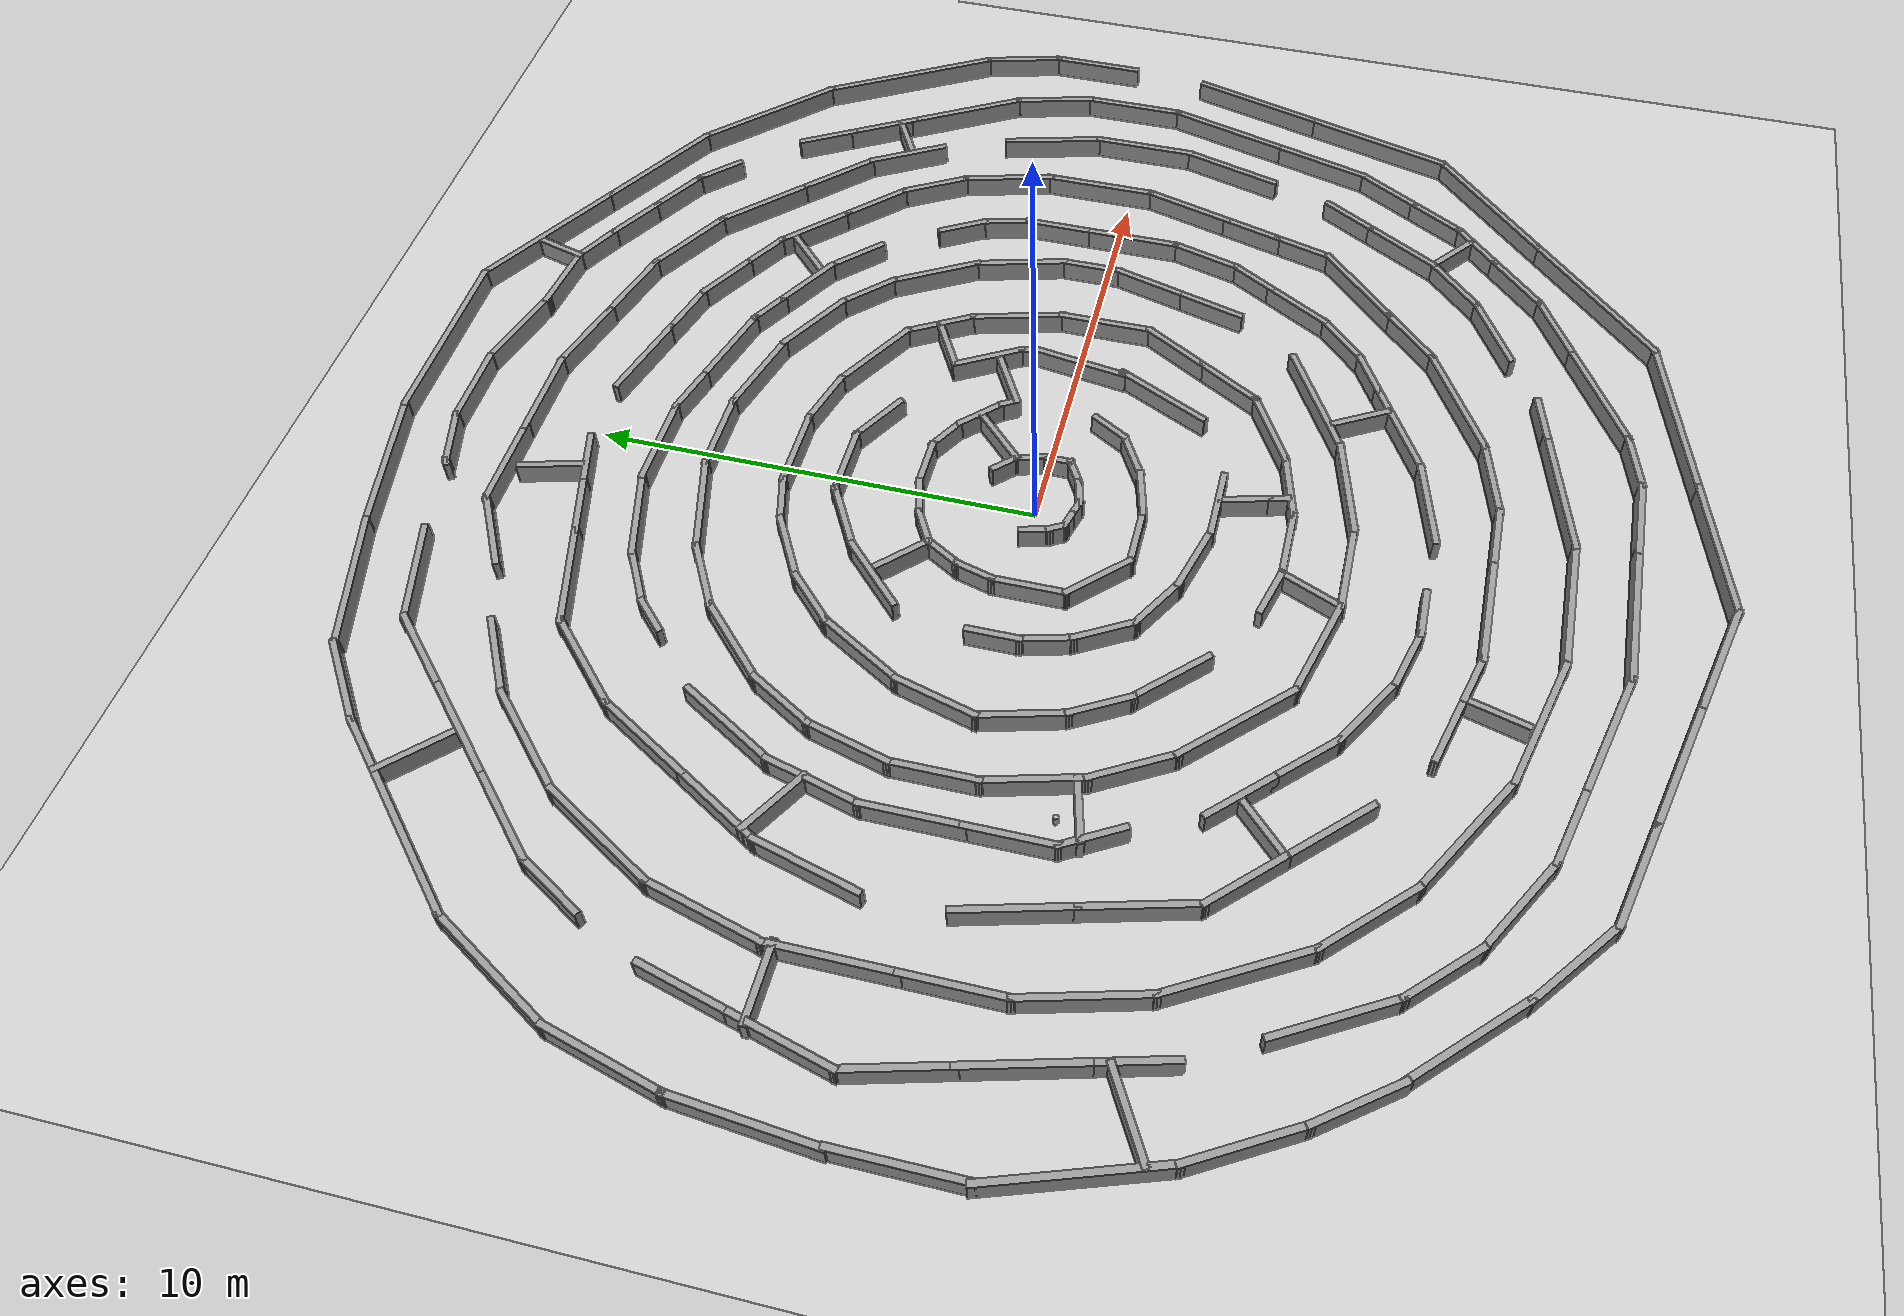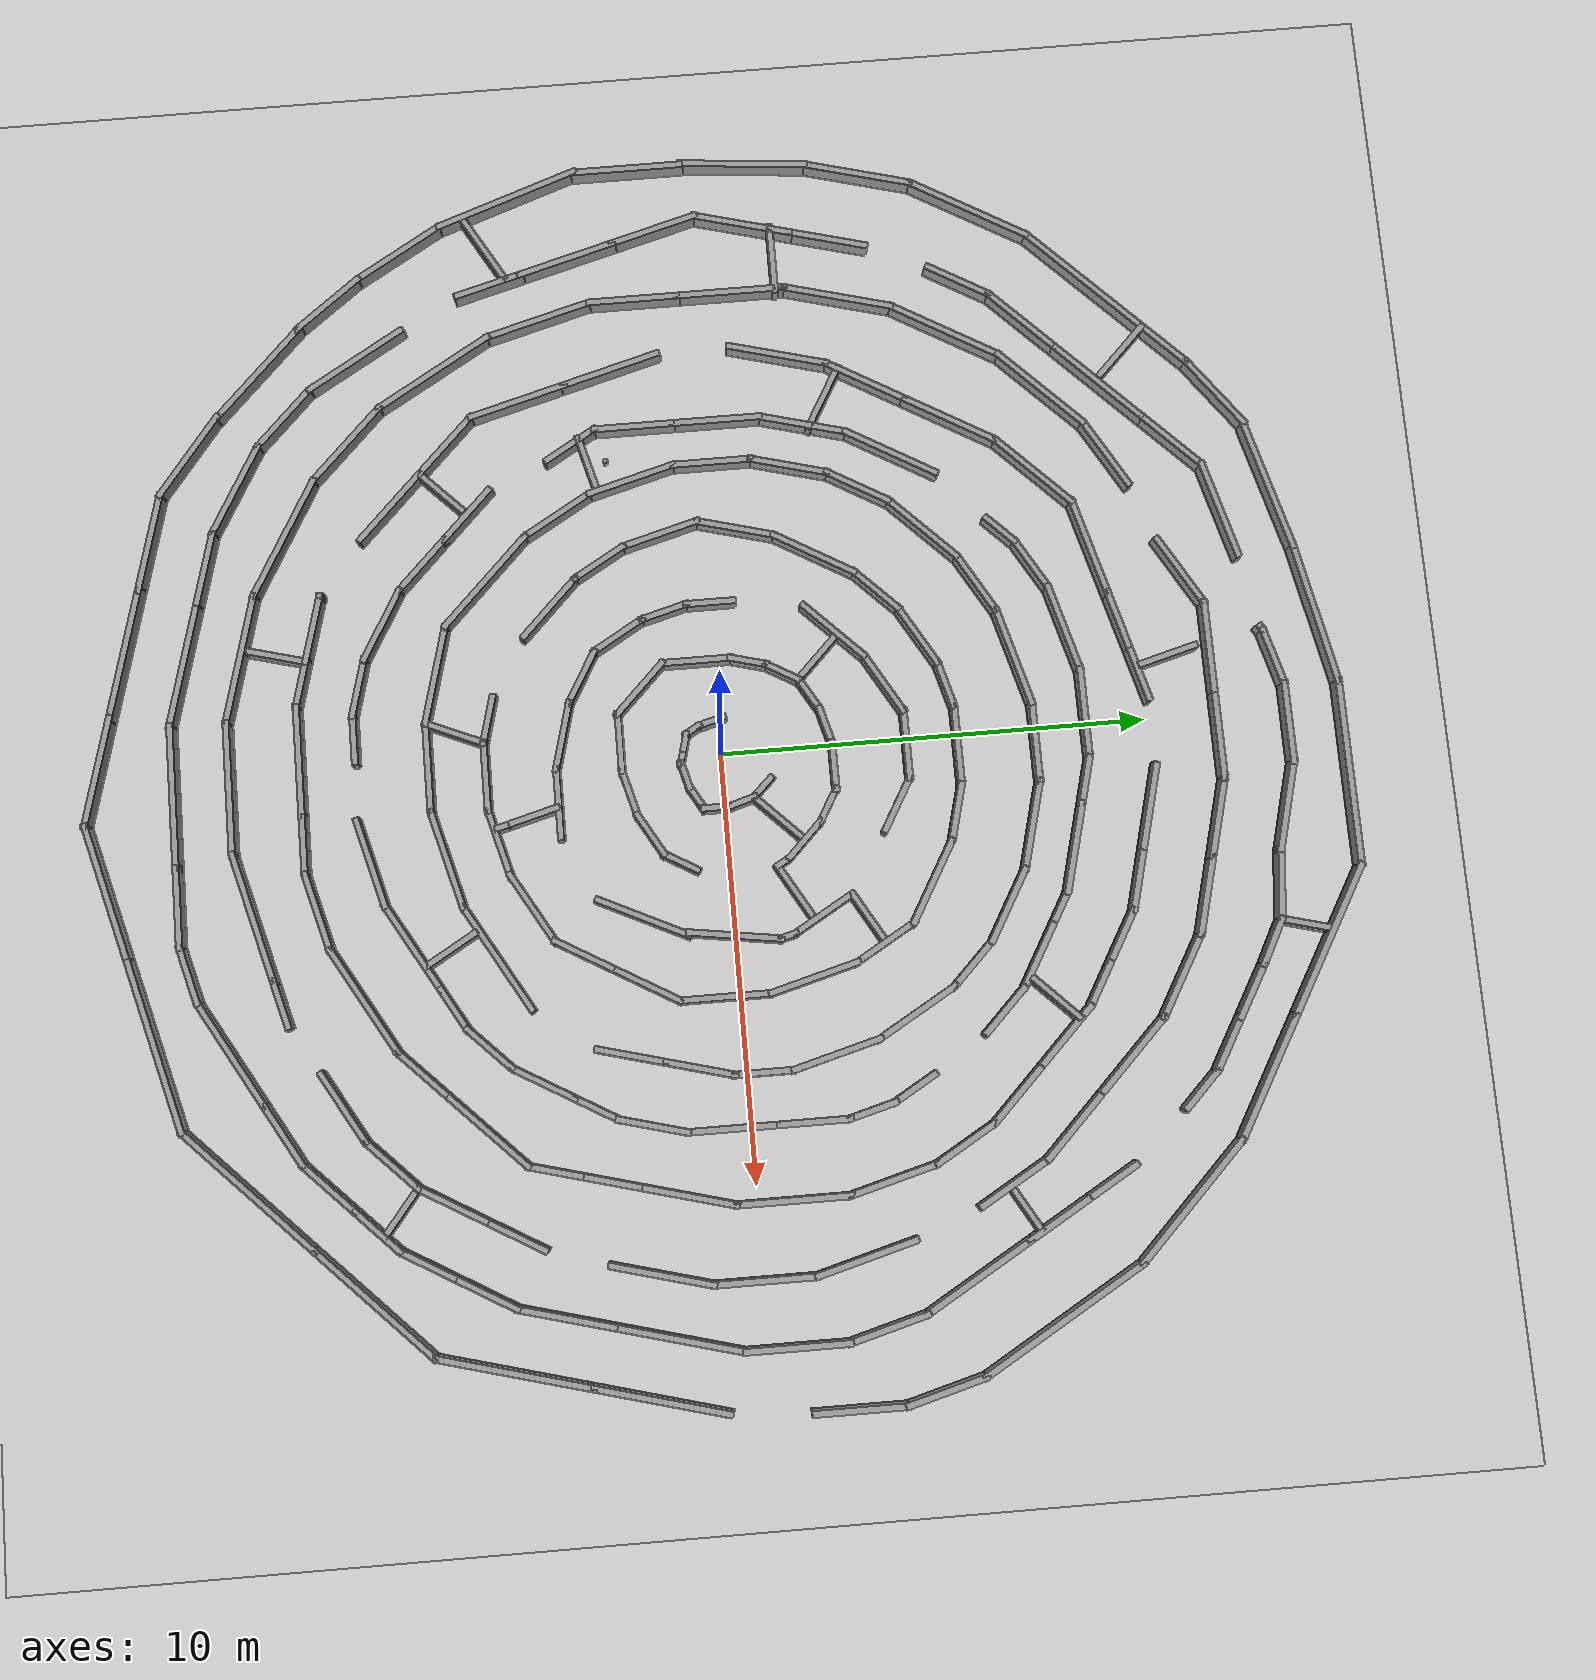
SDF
<sdf version="1.6">
 <world name="default">
  <light name="sun" type="directional">
   <pose>0 0 10 0 -0 0</pose>
   <diffuse>0.8 0.8 0.8 1</diffuse>
   <specular>0.1 0.1 0.1 1</specular>
   <attenuation>
    <range>1000</range>
    <constant>0.9</constant>
    <linear>0.01</linear>
    <quadratic>0.001</quadratic>
   </attenuation>
   <direction>-0.5 0.5 -1</direction>
  </light>
  <model name="ground_plane">
   <static>1</static>
   <link name="link">
    <collision name="collision">
     <geometry><plane><normal>0 0 1</normal><size>100 100</size></plane></geometry>
     <surface><friction><ode><mu>100</mu><mu2>50</mu2></ode></friction></surface>
    </collision>
    <visual name="visual">
     <cast_shadows>0</cast_shadows>
     <geometry><plane><normal>0 0 1</normal><size>100 100</size></plane></geometry>
     <material>
      <script><uri>file://media/materials/scripts/gazebo.material</uri><name>Gazebo/Grey</name></script>
     </material>
    </visual>
   </link>
  </model>
  <gravity>0 0 -9.8</gravity>
  <magnetic_field>6e-06 2.3e-05 -4.2e-05</magnetic_field>
  <atmosphere type="adiabatic"/>
  <physics name="default_physics" default="0" type="ode">
   <max_step_size>0.001</max_step_size>
   <real_time_factor>1</real_time_factor>
   <real_time_update_rate>1000</real_time_update_rate>
  </physics>
  <scene><ambient>0.4 0.4 0.4 1</ambient><background>0.7 0.7 0.7 1</background><shadows>1</shadows></scene>
  <spherical_coordinates>
   <surface_model>EARTH_WGS84</surface_model>
   <latitude_deg>0</latitude_deg>
   <longitude_deg>0</longitude_deg>
   <elevation>0</elevation>
   <heading_deg>0</heading_deg>
  </spherical_coordinates>
  <model name="laby4">
   <pose>-11.3155 -0.151712 0 0 -0 0</pose>
   <link name="Wall_100">
    <collision name="Wall_100_Collision">
     <geometry><box><size>3 0.15 0.5</size></box></geometry>
     <pose>0 0 0.25 0 -0 0</pose>
    </collision>
    <visual name="Wall_100_Visual">
     <pose>0 0 0.25 0 -0 0</pose>
     <geometry><box><size>3 0.15 0.5</size></box></geometry>
     <material>
      <script><uri>file://media/materials/scripts/gazebo.material</uri><name>Gazebo/Grey</name></script>
      <ambient>1 1 1 1</ambient>
     </material>
    </visual>
    <pose>1.51802 6.32561 0 0 0 -2.0944</pose>
   </link>
   <link name="Wall_101">
    <collision name="Wall_101_Collision">
     <geometry><box><size>2.75 0.15 0.5</size></box></geometry>
     <pose>0 0 0.25 0 -0 0</pose>
    </collision>
    <visual name="Wall_101_Visual">
     <pose>0 0 0.25 0 -0 0</pose>
     <geometry><box><size>2.75 0.15 0.5</size></box></geometry>
     <material>
      <script><uri>file://media/materials/scripts/gazebo.material</uri><name>Gazebo/Grey</name></script>
      <ambient>1 1 1 1</ambient>
     </material>
    </visual>
    <pose>0.469052 3.83582 0 0 0 -1.8326</pose>
   </link>
   <link name="Wall_102">
    <collision name="Wall_102_Collision">
     <geometry><box><size>2.75 0.15 0.5</size></box></geometry>
     <pose>0 0 0.25 0 -0 0</pose>
    </collision>
    <visual name="Wall_102_Visual">
     <pose>0 0 0.25 0 -0 0</pose>
     <geometry><box><size>2.75 0.15 0.5</size></box></geometry>
     <material>
      <script><uri>file://media/materials/scripts/gazebo.material</uri><name>Gazebo/Grey</name></script>
      <ambient>1 1 1 1</ambient>
     </material>
    </visual>
    <pose>0.132587 1.28012 0 0 0 -1.5708</pose>
   </link>
   <link name="Wall_103">
    <collision name="Wall_103_Collision">
     <geometry><box><size>2.25 0.15 0.5</size></box></geometry>
     <pose>0 0 0.25 0 -0 0</pose>
    </collision>
    <visual name="Wall_103_Visual">
     <pose>0 0 0.25 0 -0 0</pose>
     <geometry><box><size>2.25 0.15 0.5</size></box></geometry>
     <material>
      <script><uri>file://media/materials/scripts/gazebo.material</uri><name>Gazebo/Grey</name></script>
      <ambient>1 1 1 1</ambient>
     </material>
    </visual>
    <pose>0.132587 -1.06988 0 0 0 -1.5708</pose>
   </link>
   <link name="Wall_104">
    <collision name="Wall_104_Collision">
     <geometry><box><size>2.75 0.15 0.5</size></box></geometry>
     <pose>0 0 0.25 0 -0 0</pose>
    </collision>
    <visual name="Wall_104_Visual">
     <pose>0 0 0.25 0 -0 0</pose>
     <geometry><box><size>2.75 0.15 0.5</size></box></geometry>
     <material>
      <script><uri>file://media/materials/scripts/gazebo.material</uri><name>Gazebo/Grey</name></script>
      <ambient>1 1 1 1</ambient>
     </material>
    </visual>
    <pose>0.469052 -3.37558 0 0 0 -1.309</pose>
   </link>
   <link name="Wall_106">
    <collision name="Wall_106_Collision">
     <geometry><box><size>3.25 0.15 0.5</size></box></geometry>
     <pose>0 0 0.25 0 -0 0</pose>
    </collision>
    <visual name="Wall_106_Visual">
     <pose>0 0 0.25 0 -0 0</pose>
     <geometry><box><size>3.25 0.15 0.5</size></box></geometry>
     <material>
      <script><uri>file://media/materials/scripts/gazebo.material</uri><name>Gazebo/Grey</name></script>
      <ambient>1 1 1 1</ambient>
     </material>
    </visual>
    <pose>1.58052 -5.97363 0 0 0 -1.0472</pose>
   </link>
   <link name="Wall_107">
    <collision name="Wall_107_Collision">
     <geometry><box><size>2.5 0.15 0.5</size></box></geometry>
     <pose>0 0 0.25 0 -0 0</pose>
    </collision>
    <visual name="Wall_107_Visual">
     <pose>0 0 0.25 0 -0 0</pose>
     <geometry><box><size>2.5 0.15 0.5</size></box></geometry>
     <material>
      <script><uri>file://media/materials/scripts/gazebo.material</uri><name>Gazebo/Grey</name></script>
      <ambient>1 1 1 1</ambient>
     </material>
    </visual>
    <pose>3.18637 -8.14682 0 0 0 -0.785398</pose>
   </link>
   <link name="Wall_108">
    <collision name="Wall_108_Collision">
     <geometry><box><size>3.25 0.15 0.5</size></box></geometry>
     <pose>0 0 0.25 0 -0 0</pose>
    </collision>
    <visual name="Wall_108_Visual">
     <pose>0 0 0.25 0 -0 0</pose>
     <geometry><box><size>3.25 0.15 0.5</size></box></geometry>
     <material>
      <script><uri>file://media/materials/scripts/gazebo.material</uri><name>Gazebo/Grey</name></script>
      <ambient>1 1 1 1</ambient>
     </material>
    </visual>
    <pose>5.35956 -9.75267 0 0 0 -0.523599</pose>
   </link>
   <link name="Wall_109">
    <collision name="Wall_109_Collision">
     <geometry><box><size>3.25 0.15 0.5</size></box></geometry>
     <pose>0 0 0.25 0 -0 0</pose>
    </collision>
    <visual name="Wall_109_Visual">
     <pose>0 0 0.25 0 -0 0</pose>
     <geometry><box><size>3.25 0.15 0.5</size></box></geometry>
     <material>
      <script><uri>file://media/materials/scripts/gazebo.material</uri><name>Gazebo/Grey</name></script>
      <ambient>1 1 1 1</ambient>
     </material>
    </visual>
    <pose>8.19908 -10.9288 0 0 0 -0.261799</pose>
   </link>
   <link name="Wall_110">
    <collision name="Wall_110_Collision">
     <geometry><box><size>3.25 0.15 0.5</size></box></geometry>
     <pose>0 0 0.25 0 -0 0</pose>
    </collision>
    <visual name="Wall_110_Visual">
     <pose>0 0 0.25 0 -0 0</pose>
     <geometry><box><size>3.25 0.15 0.5</size></box></geometry>
     <material>
      <script><uri>file://media/materials/scripts/gazebo.material</uri><name>Gazebo/Grey</name></script>
      <ambient>1 1 1 1</ambient>
     </material>
    </visual>
    <pose>11.2463 -11.33 0 0 -0 0</pose>
   </link>
   <link name="Wall_111">
    <collision name="Wall_111_Collision">
     <geometry><box><size>3.25 0.15 0.5</size></box></geometry>
     <pose>0 0 0.25 0 -0 0</pose>
    </collision>
    <visual name="Wall_111_Visual">
     <pose>0 0 0.25 0 -0 0</pose>
     <geometry><box><size>3.25 0.15 0.5</size></box></geometry>
     <material>
      <script><uri>file://media/materials/scripts/gazebo.material</uri><name>Gazebo/Grey</name></script>
      <ambient>1 1 1 1</ambient>
     </material>
    </visual>
    <pose>14.2935 -10.9288 0 0 -0 0.261799</pose>
   </link>
   <link name="Wall_112">
    <collision name="Wall_112_Collision">
     <geometry><box><size>1.25 0.15 0.5</size></box></geometry>
     <pose>0 0 0.25 0 -0 0</pose>
    </collision>
    <visual name="Wall_112_Visual">
     <pose>0 0 0.25 0 -0 0</pose>
     <geometry><box><size>1.25 0.15 0.5</size></box></geometry>
     <material>
      <script><uri>file://media/materials/scripts/gazebo.material</uri><name>Gazebo/Grey</name></script>
      <ambient>1 1 1 1</ambient>
     </material>
    </visual>
    <pose>16.3219 -10.3853 0 0 -0 0.261799</pose>
   </link>
   <link name="Wall_114">
    <collision name="Wall_114_Collision">
     <geometry><box><size>2 0.15 0.5</size></box></geometry>
     <pose>0 0 0.25 0 -0 0</pose>
    </collision>
    <visual name="Wall_114_Visual">
     <pose>0 0 0.25 0 -0 0</pose>
     <geometry><box><size>2 0.15 0.5</size></box></geometry>
     <material>
      <script><uri>file://media/materials/scripts/gazebo.material</uri><name>Gazebo/Grey</name></script>
      <ambient>1 1 1 1</ambient>
     </material>
    </visual>
    <pose>18.7972 -9.08348 0 0 -0 0.523599</pose>
   </link>
   <link name="Wall_115">
    <collision name="Wall_115_Collision">
     <geometry><box><size>1.75 0.15 0.5</size></box></geometry>
     <pose>0 0 0.25 0 -0 0</pose>
    </collision>
    <visual name="Wall_115_Visual">
     <pose>0 0 0.25 0 -0 0</pose>
     <geometry><box><size>1.75 0.15 0.5</size></box></geometry>
     <material>
      <script><uri>file://media/materials/scripts/gazebo.material</uri><name>Gazebo/Grey</name></script>
      <ambient>1 1 1 1</ambient>
     </material>
    </visual>
    <pose>20.164 -8.0553 0 0 -0 0.785398</pose>
   </link>
   <link name="Wall_116">
    <collision name="Wall_116_Collision">
     <geometry><box><size>2 0.15 0.5</size></box></geometry>
     <pose>0 0 0.25 0 -0 0</pose>
    </collision>
    <visual name="Wall_116_Visual">
     <pose>0 0 0.25 0 -0 0</pose>
     <geometry><box><size>2 0.15 0.5</size></box></geometry>
     <material>
      <script><uri>file://media/materials/scripts/gazebo.material</uri><name>Gazebo/Grey</name></script>
      <ambient>1 1 1 1</ambient>
     </material>
    </visual>
    <pose>21.1922 -6.68854 0 0 -0 1.0472</pose>
   </link>
   <link name="Wall_117">
    <collision name="Wall_117_Collision">
     <geometry><box><size>1.5 0.15 0.5</size></box></geometry>
     <pose>0 0 0.25 0 -0 0</pose>
    </collision>
    <visual name="Wall_117_Visual">
     <pose>0 0 0.25 0 -0 0</pose>
     <geometry><box><size>1.5 0.15 0.5</size></box></geometry>
     <material>
      <script><uri>file://media/materials/scripts/gazebo.material</uri><name>Gazebo/Grey</name></script>
      <ambient>1 1 1 1</ambient>
     </material>
    </visual>
    <pose>21.9922 -5.3029 0 0 -0 1.0472</pose>
   </link>
   <link name="Wall_119">
    <collision name="Wall_119_Collision">
     <geometry><box><size>2.5 0.15 0.5</size></box></geometry>
     <pose>0 0 0.25 0 -0 0</pose>
    </collision>
    <visual name="Wall_119_Visual">
     <pose>0 0 0.25 0 -0 0</pose>
     <geometry><box><size>2.5 0.15 0.5</size></box></geometry>
     <material>
      <script><uri>file://media/materials/scripts/gazebo.material</uri><name>Gazebo/Grey</name></script>
      <ambient>1 1 1 1</ambient>
     </material>
    </visual>
    <pose>23.0965 -2.13355 0 0 -0 1.309</pose>
   </link>
   <link name="Wall_120">
    <collision name="Wall_120_Collision">
     <geometry><box><size>2.5 0.15 0.5</size></box></geometry>
     <pose>0 0 0.25 0 -0 0</pose>
    </collision>
    <visual name="Wall_120_Visual">
     <pose>0 0 0.25 0 -0 0</pose>
     <geometry><box><size>2.5 0.15 0.5</size></box></geometry>
     <material>
      <script><uri>file://media/materials/scripts/gazebo.material</uri><name>Gazebo/Grey</name></script>
      <ambient>1 1 1 1</ambient>
     </material>
    </visual>
    <pose>23.4006 0.176411 0 0 -0 1.5708</pose>
   </link>
   <link name="Wall_121">
    <collision name="Wall_121_Collision">
     <geometry><box><size>2.5 0.15 0.5</size></box></geometry>
     <pose>0 0 0.25 0 -0 0</pose>
    </collision>
    <visual name="Wall_121_Visual">
     <pose>0 0 0.25 0 -0 0</pose>
     <geometry><box><size>2.5 0.15 0.5</size></box></geometry>
     <material>
      <script><uri>file://media/materials/scripts/gazebo.material</uri><name>Gazebo/Grey</name></script>
      <ambient>1 1 1 1</ambient>
     </material>
    </visual>
    <pose>23.0965 2.48637 0 0 -0 1.8326</pose>
   </link>
   <link name="Wall_123">
    <collision name="Wall_123_Collision">
     <geometry><box><size>2 0.15 0.5</size></box></geometry>
     <pose>0 0 0.25 0 -0 0</pose>
    </collision>
    <visual name="Wall_123_Visual">
     <pose>0 0 0.25 0 -0 0</pose>
     <geometry><box><size>2 0.15 0.5</size></box></geometry>
     <material>
      <script><uri>file://media/materials/scripts/gazebo.material</uri><name>Gazebo/Grey</name></script>
      <ambient>1 1 1 1</ambient>
     </material>
    </visual>
    <pose>21.7097 5.9947 0 0 -0 2.0944</pose>
   </link>
   <link name="Wall_124">
    <collision name="Wall_124_Collision">
     <geometry><box><size>2 0.15 0.5</size></box></geometry>
     <pose>0 0 0.25 0 -0 0</pose>
    </collision>
    <visual name="Wall_124_Visual">
     <pose>0 0 0.25 0 -0 0</pose>
     <geometry><box><size>2 0.15 0.5</size></box></geometry>
     <material>
      <script><uri>file://media/materials/scripts/gazebo.material</uri><name>Gazebo/Grey</name></script>
      <ambient>1 1 1 1</ambient>
     </material>
    </visual>
    <pose>20.5931 7.44984 0 0 -0 2.35619</pose>
   </link>
   <link name="Wall_125">
    <collision name="Wall_125_Collision">
     <geometry><box><size>2.5 0.15 0.5</size></box></geometry>
     <pose>0 0 0.25 0 -0 0</pose>
    </collision>
    <visual name="Wall_125_Visual">
     <pose>0 0 0.25 0 -0 0</pose>
     <geometry><box><size>2.5 0.15 0.5</size></box></geometry>
     <material>
      <script><uri>file://media/materials/scripts/gazebo.material</uri><name>Gazebo/Grey</name></script>
      <ambient>1 1 1 1</ambient>
     </material>
    </visual>
    <pose>19.1082 8.93477 0 0 -0 2.35619</pose>
   </link>
   <link name="Wall_126">
    <collision name="Wall_126_Collision">
     <geometry><box><size>2.25 0.15 0.5</size></box></geometry>
     <pose>0 0 0.25 0 -0 0</pose>
    </collision>
    <visual name="Wall_126_Visual">
     <pose>0 0 0.25 0 -0 0</pose>
     <geometry><box><size>2.25 0.15 0.5</size></box></geometry>
     <material>
      <script><uri>file://media/materials/scripts/gazebo.material</uri><name>Gazebo/Grey</name></script>
      <ambient>1 1 1 1</ambient>
     </material>
    </visual>
    <pose>17.368 10.2906 0 0 -0 2.61799</pose>
   </link>
   <link name="Wall_127">
    <collision name="Wall_127_Collision">
     <geometry><box><size>2 0.15 0.5</size></box></geometry>
     <pose>0 0 0.25 0 -0 0</pose>
    </collision>
    <visual name="Wall_127_Visual">
     <pose>0 0 0.25 0 -0 0</pose>
     <geometry><box><size>2 0.15 0.5</size></box></geometry>
     <material>
      <script><uri>file://media/materials/scripts/gazebo.material</uri><name>Gazebo/Grey</name></script>
      <ambient>1 1 1 1</ambient>
     </material>
    </visual>
    <pose>15.5652 11.055 0 0 -0 2.87979</pose>
   </link>
   <link name="Wall_128">
    <collision name="Wall_128_Collision">
     <geometry><box><size>2 0.15 0.5</size></box></geometry>
     <pose>0 0 0.25 0 -0 0</pose>
    </collision>
    <visual name="Wall_128_Visual">
     <pose>0 0 0.25 0 -0 0</pose>
     <geometry><box><size>2 0.15 0.5</size></box></geometry>
     <material>
      <script><uri>file://media/materials/scripts/gazebo.material</uri><name>Gazebo/Grey</name></script>
      <ambient>1 1 1 1</ambient>
     </material>
    </visual>
    <pose>13.7783 11.5338 0 0 -0 2.87979</pose>
   </link>
   <link name="Wall_129">
    <collision name="Wall_129_Collision">
     <geometry><box><size>2.25 0.15 0.5</size></box></geometry>
     <pose>0 0 0.25 0 -0 0</pose>
    </collision>
    <visual name="Wall_129_Visual">
     <pose>0 0 0.25 0 -0 0</pose>
     <geometry><box><size>2.25 0.15 0.5</size></box></geometry>
     <material>
      <script><uri>file://media/materials/scripts/gazebo.material</uri><name>Gazebo/Grey</name></script>
      <ambient>1 1 1 1</ambient>
     </material>
    </visual>
    <pose>11.8348 11.7732 0 0 -0 3.14159</pose>
   </link>
   <link name="Wall_130">
    <collision name="Wall_130_Collision">
     <geometry><box><size>2.25 0.15 0.5</size></box></geometry>
     <pose>0 0 0.25 0 -0 0</pose>
    </collision>
    <visual name="Wall_130_Visual">
     <pose>0 0 0.25 0 -0 0</pose>
     <geometry><box><size>2.25 0.15 0.5</size></box></geometry>
     <material>
      <script><uri>file://media/materials/scripts/gazebo.material</uri><name>Gazebo/Grey</name></script>
      <ambient>1 1 1 1</ambient>
     </material>
    </visual>
    <pose>9.73478 11.7732 0 0 -0 3.14159</pose>
   </link>
   <link name="Wall_131">
    <collision name="Wall_131_Collision">
     <geometry><box><size>2 0.15 0.5</size></box></geometry>
     <pose>0 0 0.25 0 -0 0</pose>
    </collision>
    <visual name="Wall_131_Visual">
     <pose>0 0 0.25 0 -0 0</pose>
     <geometry><box><size>2 0.15 0.5</size></box></geometry>
     <material>
      <script><uri>file://media/materials/scripts/gazebo.material</uri><name>Gazebo/Grey</name></script>
      <ambient>1 1 1 1</ambient>
     </material>
    </visual>
    <pose>7.8837 11.3107 0 0 0 -2.61799</pose>
   </link>
   <link name="Wall_133">
    <collision name="Wall_133_Collision">
     <geometry><box><size>1.75 0.15 0.5</size></box></geometry>
     <pose>0 0 0.25 0 -0 0</pose>
    </collision>
    <visual name="Wall_133_Visual">
     <pose>0 0 0.25 0 -0 0</pose>
     <geometry><box><size>1.75 0.15 0.5</size></box></geometry>
     <material>
      <script><uri>file://media/materials/scripts/gazebo.material</uri><name>Gazebo/Grey</name></script>
      <ambient>1 1 1 1</ambient>
     </material>
    </visual>
    <pose>-0.623102 2.36168 0 0 -0 0</pose>
   </link>
   <link name="Wall_135">
    <collision name="Wall_135_Collision">
     <geometry><box><size>1.25 0.15 0.5</size></box></geometry>
     <pose>0 0 0.25 0 -0 0</pose>
    </collision>
    <visual name="Wall_135_Visual">
     <pose>0 0 0.25 0 -0 0</pose>
     <geometry><box><size>1.25 0.15 0.5</size></box></geometry>
     <material>
      <script><uri>file://media/materials/scripts/gazebo.material</uri><name>Gazebo/Grey</name></script>
      <ambient>1 1 1 1</ambient>
     </material>
    </visual>
    <pose>22.2992 6.17957 0 0 0 -2.61799</pose>
   </link>
   <link name="Wall_137">
    <collision name="Wall_137_Collision">
     <geometry><box><size>1.38704 0.15 0.5</size></box></geometry>
     <pose>0 0 0.25 0 -0 0</pose>
    </collision>
    <visual name="Wall_137_Visual">
     <pose>0 0 0.25 0 -0 0</pose>
     <geometry><box><size>1.38704 0.15 0.5</size></box></geometry>
     <material>
      <script><uri>file://media/materials/scripts/gazebo.material</uri><name>Gazebo/Grey</name></script>
      <ambient>1 1 1 1</ambient>
     </material>
    </visual>
    <pose>21.2119 -7.87689 0 0 -0 2.46501</pose>
   </link>
   <link name="Wall_140">
    <collision name="Wall_140_Collision">
     <geometry><box><size>2.25 0.15 0.5</size></box></geometry>
     <pose>0 0 0.25 0 -0 0</pose>
    </collision>
    <visual name="Wall_140_Visual">
     <pose>0 0 0.25 0 -0 0</pose>
     <geometry><box><size>2.25 0.15 0.5</size></box></geometry>
     <material>
      <script><uri>file://media/materials/scripts/gazebo.material</uri><name>Gazebo/Grey</name></script>
      <ambient>1 1 1 1</ambient>
     </material>
    </visual>
    <pose>4.81018 -7.19725 0 0 -0 2.35619</pose>
   </link>
   <link name="Wall_141">
    <collision name="Wall_141_Collision">
     <geometry><box><size>2 0.15 0.5</size></box></geometry>
     <pose>0 0 0.25 0 -0 0</pose>
    </collision>
    <visual name="Wall_141_Visual">
     <pose>0 0 0.25 0 -0 0</pose>
     <geometry><box><size>2 0.15 0.5</size></box></geometry>
     <material>
      <script><uri>file://media/materials/scripts/gazebo.material</uri><name>Gazebo/Grey</name></script>
      <ambient>1 1 1 1</ambient>
     </material>
    </visual>
    <pose>3.41365 -5.80071 0 0 -0 2.35619</pose>
   </link>
   <link name="Wall_142">
    <collision name="Wall_142_Collision">
     <geometry><box><size>2.5 0.15 0.5</size></box></geometry>
     <pose>0 0 0.25 0 -0 0</pose>
    </collision>
    <visual name="Wall_142_Visual">
     <pose>0 0 0.25 0 -0 0</pose>
     <geometry><box><size>2.5 0.15 0.5</size></box></geometry>
     <material>
      <script><uri>file://media/materials/scripts/gazebo.material</uri><name>Gazebo/Grey</name></script>
      <ambient>1 1 1 1</ambient>
     </material>
    </visual>
    <pose>2.45546 -4.01168 0 0 -0 1.8326</pose>
   </link>
   <link name="Wall_143">
    <collision name="Wall_143_Collision">
     <geometry><box><size>2.5 0.15 0.5</size></box></geometry>
     <pose>0 0 0.25 0 -0 0</pose>
    </collision>
    <visual name="Wall_143_Visual">
     <pose>0 0 0.25 0 -0 0</pose>
     <geometry><box><size>2.5 0.15 0.5</size></box></geometry>
     <material>
      <script><uri>file://media/materials/scripts/gazebo.material</uri><name>Gazebo/Grey</name></script>
      <ambient>1 1 1 1</ambient>
     </material>
    </visual>
    <pose>1.84724 -1.74175 0 0 -0 1.8326</pose>
   </link>
   <link name="Wall_145">
    <collision name="Wall_145_Collision">
     <geometry><box><size>2.5 0.15 0.5</size></box></geometry>
     <pose>0 0 0.25 0 -0 0</pose>
    </collision>
    <visual name="Wall_145_Visual">
     <pose>0 0 0.25 0 -0 0</pose>
     <geometry><box><size>2.5 0.15 0.5</size></box></geometry>
     <material>
      <script><uri>file://media/materials/scripts/gazebo.material</uri><name>Gazebo/Grey</name></script>
      <ambient>1 1 1 1</ambient>
     </material>
    </visual>
    <pose>1.80109 2.27995 0 0 -0 1.309</pose>
   </link>
   <link name="Wall_146">
    <collision name="Wall_146_Collision">
     <geometry><box><size>2.25 0.15 0.5</size></box></geometry>
     <pose>0 0 0.25 0 -0 0</pose>
    </collision>
    <visual name="Wall_146_Visual">
     <pose>0 0 0.25 0 -0 0</pose>
     <geometry><box><size>2.25 0.15 0.5</size></box></geometry>
     <material>
      <script><uri>file://media/materials/scripts/gazebo.material</uri><name>Gazebo/Grey</name></script>
      <ambient>1 1 1 1</ambient>
     </material>
    </visual>
    <pose>2.6302 4.32423 0 0 -0 1.0472</pose>
   </link>
   <link name="Wall_147">
    <collision name="Wall_147_Collision">
     <geometry><box><size>2.5 0.15 0.5</size></box></geometry>
     <pose>0 0 0.25 0 -0 0</pose>
    </collision>
    <visual name="Wall_147_Visual">
     <pose>0 0 0.25 0 -0 0</pose>
     <geometry><box><size>2.5 0.15 0.5</size></box></geometry>
     <material>
      <script><uri>file://media/materials/scripts/gazebo.material</uri><name>Gazebo/Grey</name></script>
      <ambient>1 1 1 1</ambient>
     </material>
    </visual>
    <pose>3.7427 6.25114 0 0 -0 1.0472</pose>
   </link>
   <link name="Wall_148">
    <collision name="Wall_148_Collision">
     <geometry><box><size>2.5 0.15 0.5</size></box></geometry>
     <pose>0 0 0.25 0 -0 0</pose>
    </collision>
    <visual name="Wall_148_Visual">
     <pose>0 0 0.25 0 -0 0</pose>
     <geometry><box><size>2.5 0.15 0.5</size></box></geometry>
     <material>
      <script><uri>file://media/materials/scripts/gazebo.material</uri><name>Gazebo/Grey</name></script>
      <ambient>1 1 1 1</ambient>
     </material>
    </visual>
    <pose>5.16105 8.09957 0 0 -0 0.785398</pose>
   </link>
   <link name="Wall_149">
    <collision name="Wall_149_Collision">
     <geometry><box><size>2.5 0.15 0.5</size></box></geometry>
     <pose>0 0 0.25 0 -0 0</pose>
    </collision>
    <visual name="Wall_149_Visual">
     <pose>0 0 0.25 0 -0 0</pose>
     <geometry><box><size>2.5 0.15 0.5</size></box></geometry>
     <material>
      <script><uri>file://media/materials/scripts/gazebo.material</uri><name>Gazebo/Grey</name></script>
      <ambient>1 1 1 1</ambient>
     </material>
    </visual>
    <pose>7.12687 9.23453 0 0 -0 0.261799</pose>
   </link>
   <link name="Wall_150">
    <collision name="Wall_150_Collision">
     <geometry><box><size>1.5 0.15 0.5</size></box></geometry>
     <pose>0 0 0.25 0 -0 0</pose>
    </collision>
    <visual name="Wall_150_Visual">
     <pose>0 0 0.25 0 -0 0</pose>
     <geometry><box><size>1.5 0.15 0.5</size></box></geometry>
     <material>
      <script><uri>file://media/materials/scripts/gazebo.material</uri><name>Gazebo/Grey</name></script>
      <ambient>1 1 1 1</ambient>
     </material>
    </visual>
    <pose>8.91383 9.71335 0 0 -0 0.261799</pose>
   </link>
   <link name="Wall_151">
    <collision name="Wall_151_Collision">
     <geometry><box><size>1.5 0.15 0.5</size></box></geometry>
     <pose>0 0 0.25 0 -0 0</pose>
    </collision>
    <visual name="Wall_151_Visual">
     <pose>0 0 0.25 0 -0 0</pose>
     <geometry><box><size>1.5 0.15 0.5</size></box></geometry>
     <material>
      <script><uri>file://media/materials/scripts/gazebo.material</uri><name>Gazebo/Grey</name></script>
      <ambient>1 1 1 1</ambient>
     </material>
    </visual>
    <pose>10.2178 10.0628 0 0 -0 0.261799</pose>
   </link>
   <link name="Wall_153">
    <collision name="Wall_153_Collision">
     <geometry><box><size>2.25 0.15 0.5</size></box></geometry>
     <pose>0 0 0.25 0 -0 0</pose>
    </collision>
    <visual name="Wall_153_Visual">
     <pose>0 0 0.25 0 -0 0</pose>
     <geometry><box><size>2.25 0.15 0.5</size></box></geometry>
     <material>
      <script><uri>file://media/materials/scripts/gazebo.material</uri><name>Gazebo/Grey</name></script>
      <ambient>1 1 1 1</ambient>
     </material>
    </visual>
    <pose>13.4615 9.95791 0 0 0 -0.261799</pose>
   </link>
   <link name="Wall_154">
    <collision name="Wall_154_Collision">
     <geometry><box><size>1.5 0.15 0.5</size></box></geometry>
     <pose>0 0 0.25 0 -0 0</pose>
    </collision>
    <visual name="Wall_154_Visual">
     <pose>0 0 0.25 0 -0 0</pose>
     <geometry><box><size>1.5 0.15 0.5</size></box></geometry>
     <material>
      <script><uri>file://media/materials/scripts/gazebo.material</uri><name>Gazebo/Grey</name></script>
      <ambient>1 1 1 1</ambient>
     </material>
    </visual>
    <pose>15.1277 9.51145 0 0 0 -0.261799</pose>
   </link>
   <link name="Wall_155">
    <collision name="Wall_155_Collision">
     <geometry><box><size>1.5 0.15 0.5</size></box></geometry>
     <pose>0 0 0.25 0 -0 0</pose>
    </collision>
    <visual name="Wall_155_Visual">
     <pose>0 0 0.25 0 -0 0</pose>
     <geometry><box><size>1.5 0.15 0.5</size></box></geometry>
     <material>
      <script><uri>file://media/materials/scripts/gazebo.material</uri><name>Gazebo/Grey</name></script>
      <ambient>1 1 1 1</ambient>
     </material>
    </visual>
    <pose>16.3643 8.99925 0 0 0 -0.523599</pose>
   </link>
   <link name="Wall_156">
    <collision name="Wall_156_Collision">
     <geometry><box><size>1.25 0.15 0.5</size></box></geometry>
     <pose>0 0 0.25 0 -0 0</pose>
    </collision>
    <visual name="Wall_156_Visual">
     <pose>0 0 0.25 0 -0 0</pose>
     <geometry><box><size>1.25 0.15 0.5</size></box></geometry>
     <material>
      <script><uri>file://media/materials/scripts/gazebo.material</uri><name>Gazebo/Grey</name></script>
      <ambient>1 1 1 1</ambient>
     </material>
    </visual>
    <pose>17.4252 8.38675 0 0 0 -0.523599</pose>
   </link>
   <link name="Wall_157">
    <collision name="Wall_157_Collision">
     <geometry><box><size>2 0.15 0.5</size></box></geometry>
     <pose>0 0 0.25 0 -0 0</pose>
    </collision>
    <visual name="Wall_157_Visual">
     <pose>0 0 0.25 0 -0 0</pose>
     <geometry><box><size>2 0.15 0.5</size></box></geometry>
     <material>
      <script><uri>file://media/materials/scripts/gazebo.material</uri><name>Gazebo/Grey</name></script>
      <ambient>1 1 1 1</ambient>
     </material>
    </visual>
    <pose>18.5556 7.45768 0 0 0 -0.785398</pose>
   </link>
   <link name="Wall_158">
    <collision name="Wall_158_Collision">
     <geometry><box><size>1.75 0.15 0.5</size></box></geometry>
     <pose>0 0 0.25 0 -0 0</pose>
    </collision>
    <visual name="Wall_158_Visual">
     <pose>0 0 0.25 0 -0 0</pose>
     <geometry><box><size>1.75 0.15 0.5</size></box></geometry>
     <material>
      <script><uri>file://media/materials/scripts/gazebo.material</uri><name>Gazebo/Grey</name></script>
      <ambient>1 1 1 1</ambient>
     </material>
    </visual>
    <pose>19.7753 6.23792 0 0 0 -0.785398</pose>
   </link>
   <link name="Wall_159">
    <collision name="Wall_159_Collision">
     <geometry><box><size>1.75 0.15 0.5</size></box></geometry>
     <pose>0 0 0.25 0 -0 0</pose>
    </collision>
    <visual name="Wall_159_Visual">
     <pose>0 0 0.25 0 -0 0</pose>
     <geometry><box><size>1.75 0.15 0.5</size></box></geometry>
     <material>
      <script><uri>file://media/materials/scripts/gazebo.material</uri><name>Gazebo/Grey</name></script>
      <ambient>1 1 1 1</ambient>
     </material>
    </visual>
    <pose>20.741 4.97941 0 0 0 -1.0472</pose>
   </link>
   <link name="Wall_160">
    <collision name="Wall_160_Collision">
     <geometry><box><size>2.25 0.15 0.5</size></box></geometry>
     <pose>0 0 0.25 0 -0 0</pose>
    </collision>
    <visual name="Wall_160_Visual">
     <pose>0 0 0.25 0 -0 0</pose>
     <geometry><box><size>2.25 0.15 0.5</size></box></geometry>
     <material>
      <script><uri>file://media/materials/scripts/gazebo.material</uri><name>Gazebo/Grey</name></script>
      <ambient>1 1 1 1</ambient>
     </material>
    </visual>
    <pose>21.4128 3.27237 0 0 0 -1.309</pose>
   </link>
   <link name="Wall_162">
    <collision name="Wall_162_Collision">
     <geometry><box><size>2.75 0.15 0.5</size></box></geometry>
     <pose>0 0 0.25 0 -0 0</pose>
    </collision>
    <visual name="Wall_162_Visual">
     <pose>0 0 0.25 0 -0 0</pose>
     <geometry><box><size>2.75 0.15 0.5</size></box></geometry>
     <material>
      <script><uri>file://media/materials/scripts/gazebo.material</uri><name>Gazebo/Grey</name></script>
      <ambient>1 1 1 1</ambient>
     </material>
    </visual>
    <pose>21.6845 0.958146 0 0 0 -1.5708</pose>
   </link>
   <link name="Wall_163">
    <collision name="Wall_163_Collision">
     <geometry><box><size>2.25 0.15 0.5</size></box></geometry>
     <pose>0 0 0.25 0 -0 0</pose>
    </collision>
    <visual name="Wall_163_Visual">
     <pose>0 0 0.25 0 -0 0</pose>
     <geometry><box><size>2.25 0.15 0.5</size></box></geometry>
     <material>
      <script><uri>file://media/materials/scripts/gazebo.material</uri><name>Gazebo/Grey</name></script>
      <ambient>1 1 1 1</ambient>
     </material>
    </visual>
    <pose>21.4128 -1.35608 0 0 0 -1.8326</pose>
   </link>
   <link name="Wall_164">
    <collision name="Wall_164_Collision">
     <geometry><box><size>1.5 0.15 0.5</size></box></geometry>
     <pose>0 0 0.25 0 -0 0</pose>
    </collision>
    <visual name="Wall_164_Visual">
     <pose>0 0 0.25 0 -0 0</pose>
     <geometry><box><size>1.5 0.15 0.5</size></box></geometry>
     <material>
      <script><uri>file://media/materials/scripts/gazebo.material</uri><name>Gazebo/Grey</name></script>
      <ambient>1 1 1 1</ambient>
     </material>
    </visual>
    <pose>20.9663 -3.0223 0 0 0 -1.8326</pose>
   </link>
   <link name="Wall_165">
    <collision name="Wall_165_Collision">
     <geometry><box><size>1.5 0.15 0.5</size></box></geometry>
     <pose>0 0 0.25 0 -0 0</pose>
    </collision>
    <visual name="Wall_165_Visual">
     <pose>0 0 0.25 0 -0 0</pose>
     <geometry><box><size>1.5 0.15 0.5</size></box></geometry>
     <material>
      <script><uri>file://media/materials/scripts/gazebo.material</uri><name>Gazebo/Grey</name></script>
      <ambient>1 1 1 1</ambient>
     </material>
    </visual>
    <pose>20.6169 -4.3263 0 0 0 -1.8326</pose>
   </link>
   <link name="Wall_166">
    <collision name="Wall_166_Collision">
     <geometry><box><size>2.5 0.15 0.5</size></box></geometry>
     <pose>0 0 0.25 0 -0 0</pose>
    </collision>
    <visual name="Wall_166_Visual">
     <pose>0 0 0.25 0 -0 0</pose>
     <geometry><box><size>2.5 0.15 0.5</size></box></geometry>
     <material>
      <script><uri>file://media/materials/scripts/gazebo.material</uri><name>Gazebo/Grey</name></script>
      <ambient>1 1 1 1</ambient>
     </material>
    </visual>
    <pose>19.6113 -5.80915 0 0 0 -2.35619</pose>
   </link>
   <link name="Wall_167">
    <collision name="Wall_167_Collision">
     <geometry><box><size>1.75 0.15 0.5</size></box></geometry>
     <pose>0 0 0.25 0 -0 0</pose>
    </collision>
    <visual name="Wall_167_Visual">
     <pose>0 0 0.25 0 -0 0</pose>
     <geometry><box><size>1.75 0.15 0.5</size></box></geometry>
     <material>
      <script><uri>file://media/materials/scripts/gazebo.material</uri><name>Gazebo/Grey</name></script>
      <ambient>1 1 1 1</ambient>
     </material>
    </visual>
    <pose>18.2148 -7.20568 0 0 0 -2.35619</pose>
   </link>
   <link name="Wall_168">
    <collision name="Wall_168_Collision">
     <geometry><box><size>3 0.15 0.5</size></box></geometry>
     <pose>0 0 0.25 0 -0 0</pose>
    </collision>
    <visual name="Wall_168_Visual">
     <pose>0 0 0.25 0 -0 0</pose>
     <geometry><box><size>3 0.15 0.5</size></box></geometry>
     <material>
      <script><uri>file://media/materials/scripts/gazebo.material</uri><name>Gazebo/Grey</name></script>
      <ambient>1 1 1 1</ambient>
     </material>
    </visual>
    <pose>16.415 -8.48387 0 0 0 -2.61799</pose>
   </link>
   <link name="Wall_169">
    <collision name="Wall_169_Collision">
     <geometry><box><size>2 0.15 0.5</size></box></geometry>
     <pose>0 0 0.25 0 -0 0</pose>
    </collision>
    <visual name="Wall_169_Visual">
     <pose>0 0 0.25 0 -0 0</pose>
     <geometry><box><size>2 0.15 0.5</size></box></geometry>
     <material>
      <script><uri>file://media/materials/scripts/gazebo.material</uri><name>Gazebo/Grey</name></script>
      <ambient>1 1 1 1</ambient>
     </material>
    </visual>
    <pose>14.2875 -9.43578 0 0 0 -2.87979</pose>
   </link>
   <link name="Wall_17">
    <collision name="Wall_17_Collision">
     <geometry><box><size>3.25 0.15 0.5</size></box></geometry>
     <pose>0 0 0.25 0 -0 0</pose>
    </collision>
    <visual name="Wall_17_Visual">
     <pose>0 0 0.25 0 -0 0</pose>
     <geometry><box><size>3.25 0.15 0.5</size></box></geometry>
     <material>
      <script><uri>file://media/materials/scripts/gazebo.material</uri><name>Gazebo/Grey</name></script>
      <ambient>1 1 1 1</ambient>
     </material>
    </visual>
    <pose>25.8278 -2.3614 0 0 0 -1.8326</pose>
   </link>
   <link name="Wall_170">
    <collision name="Wall_170_Collision">
     <geometry><box><size>1.5 0.15 0.5</size></box></geometry>
     <pose>0 0 0.25 0 -0 0</pose>
    </collision>
    <visual name="Wall_170_Visual">
     <pose>0 0 0.25 0 -0 0</pose>
     <geometry><box><size>1.5 0.15 0.5</size></box></geometry>
     <material>
      <script><uri>file://media/materials/scripts/gazebo.material</uri><name>Gazebo/Grey</name></script>
      <ambient>1 1 1 1</ambient>
     </material>
    </visual>
    <pose>12.719 -9.67519 0 0 -0 3.14159</pose>
   </link>
   <link name="Wall_171">
    <collision name="Wall_171_Collision">
     <geometry><box><size>2.75 0.15 0.5</size></box></geometry>
     <pose>0 0 0.25 0 -0 0</pose>
    </collision>
    <visual name="Wall_171_Visual">
     <pose>0 0 0.25 0 -0 0</pose>
     <geometry><box><size>2.75 0.15 0.5</size></box></geometry>
     <material>
      <script><uri>file://media/materials/scripts/gazebo.material</uri><name>Gazebo/Grey</name></script>
      <ambient>1 1 1 1</ambient>
     </material>
    </visual>
    <pose>10.744 -9.67519 0 0 -0 3.14159</pose>
   </link>
   <link name="Wall_172">
    <collision name="Wall_172_Collision">
     <geometry><box><size>1.25 0.15 0.5</size></box></geometry>
     <pose>0 0 0.25 0 -0 0</pose>
    </collision>
    <visual name="Wall_172_Visual">
     <pose>0 0 0.25 0 -0 0</pose>
     <geometry><box><size>1.25 0.15 0.5</size></box></geometry>
     <material>
      <script><uri>file://media/materials/scripts/gazebo.material</uri><name>Gazebo/Grey</name></script>
      <ambient>1 1 1 1</ambient>
     </material>
    </visual>
    <pose>8.91273 -9.53284 0 0 -0 2.87979</pose>
   </link>
   <link name="Wall_173">
    <collision name="Wall_173_Collision">
     <geometry><box><size>1.75 0.15 0.5</size></box></geometry>
     <pose>0 0 0.25 0 -0 0</pose>
    </collision>
    <visual name="Wall_173_Visual">
     <pose>0 0 0.25 0 -0 0</pose>
     <geometry><box><size>1.75 0.15 0.5</size></box></geometry>
     <material>
      <script><uri>file://media/materials/scripts/gazebo.material</uri><name>Gazebo/Grey</name></script>
      <ambient>1 1 1 1</ambient>
     </material>
    </visual>
    <pose>7.60872 -9.18343 0 0 -0 2.87979</pose>
   </link>
   <link name="Wall_174">
    <collision name="Wall_174_Collision">
     <geometry><box><size>0.15 0.15 0.5</size></box></geometry>
     <pose>0 0 0.25 0 -0 0</pose>
    </collision>
    <visual name="Wall_174_Visual">
     <pose>0 0 0.25 0 -0 0</pose>
     <geometry><box><size>0.15 0.15 0.5</size></box></geometry>
     <material>
      <script><uri>file://media/materials/scripts/gazebo.material</uri><name>Gazebo/Grey</name></script>
      <ambient>1 1 1 1</ambient>
     </material>
    </visual>
    <pose>6.83598 -8.97637 0 0 -0 0</pose>
   </link>
   <link name="Wall_176">
    <collision name="Wall_176_Collision">
     <geometry><box><size>1.5 0.15 0.5</size></box></geometry>
     <pose>0 0 0.25 0 -0 0</pose>
    </collision>
    <visual name="Wall_176_Visual">
     <pose>0 0 0.25 0 -0 0</pose>
     <geometry><box><size>1.5 0.15 0.5</size></box></geometry>
     <material>
      <script><uri>file://media/materials/scripts/gazebo.material</uri><name>Gazebo/Grey</name></script>
      <ambient>1 1 1 1</ambient>
     </material>
    </visual>
    <pose>8.20676 -10.0425 0 0 0 -1.8326</pose>
   </link>
   <link name="Wall_178">
    <collision name="Wall_178_Collision">
     <geometry><box><size>1.5 0.15 0.5</size></box></geometry>
     <pose>0 0 0.25 0 -0 0</pose>
    </collision>
    <visual name="Wall_178_Visual">
     <pose>0 0 0.25 0 -0 0</pose>
     <geometry><box><size>1.5 0.15 0.5</size></box></geometry>
     <material>
      <script><uri>file://media/materials/scripts/gazebo.material</uri><name>Gazebo/Grey</name></script>
      <ambient>1 1 1 1</ambient>
     </material>
    </visual>
    <pose>9.87034 10.7893 0 0 0 -1.309</pose>
   </link>
   <link name="Wall_18">
    <collision name="Wall_18_Collision">
     <geometry><box><size>3.75 0.15 0.5</size></box></geometry>
     <pose>0 0 0.25 0 -0 0</pose>
    </collision>
    <visual name="Wall_18_Visual">
     <pose>0 0 0.25 0 -0 0</pose>
     <geometry><box><size>3.75 0.15 0.5</size></box></geometry>
     <material>
      <script><uri>file://media/materials/scripts/gazebo.material</uri><name>Gazebo/Grey</name></script>
      <ambient>1 1 1 1</ambient>
     </material>
    </visual>
    <pose>24.9608 -5.59725 0 0 0 -1.8326</pose>
   </link>
   <link name="Wall_180">
    <collision name="Wall_180_Collision">
     <geometry><box><size>2.25 0.15 0.5</size></box></geometry>
     <pose>0 0 0.25 0 -0 0</pose>
    </collision>
    <visual name="Wall_180_Visual">
     <pose>0 0 0.25 0 -0 0</pose>
     <geometry><box><size>2.25 0.15 0.5</size></box></geometry>
     <material>
      <script><uri>file://media/materials/scripts/gazebo.material</uri><name>Gazebo/Grey</name></script>
      <ambient>1 1 1 1</ambient>
     </material>
    </visual>
    <pose>13.2549 -8.14749 0 0 -0 0.261799</pose>
   </link>
   <link name="Wall_181">
    <collision name="Wall_181_Collision">
     <geometry><box><size>2.5 0.15 0.5</size></box></geometry>
     <pose>0 0 0.25 0 -0 0</pose>
    </collision>
    <visual name="Wall_181_Visual">
     <pose>0 0 0.25 0 -0 0</pose>
     <geometry><box><size>2.5 0.15 0.5</size></box></geometry>
     <material>
      <script><uri>file://media/materials/scripts/gazebo.material</uri><name>Gazebo/Grey</name></script>
      <ambient>1 1 1 1</ambient>
     </material>
    </visual>
    <pose>15.2867 -7.28823 0 0 -0 0.523599</pose>
   </link>
   <link name="Wall_182">
    <collision name="Wall_182_Collision">
     <geometry><box><size>1.25 0.15 0.5</size></box></geometry>
     <pose>0 0 0.25 0 -0 0</pose>
    </collision>
    <visual name="Wall_182_Visual">
     <pose>0 0 0.25 0 -0 0</pose>
     <geometry><box><size>1.25 0.15 0.5</size></box></geometry>
     <material>
      <script><uri>file://media/materials/scripts/gazebo.material</uri><name>Gazebo/Grey</name></script>
      <ambient>1 1 1 1</ambient>
     </material>
    </visual>
    <pose>16.7806 -6.42573 0 0 -0 0.523599</pose>
   </link>
   <link name="Wall_183">
    <collision name="Wall_183_Collision">
     <geometry><box><size>1.5 0.15 0.5</size></box></geometry>
     <pose>0 0 0.25 0 -0 0</pose>
    </collision>
    <visual name="Wall_183_Visual">
     <pose>0 0 0.25 0 -0 0</pose>
     <geometry><box><size>1.5 0.15 0.5</size></box></geometry>
     <material>
      <script><uri>file://media/materials/scripts/gazebo.material</uri><name>Gazebo/Grey</name></script>
      <ambient>1 1 1 1</ambient>
     </material>
    </visual>
    <pose>17.7342 -5.67344 0 0 -0 0.785398</pose>
   </link>
   <link name="Wall_184">
    <collision name="Wall_184_Collision">
     <geometry><box><size>1.75 0.15 0.5</size></box></geometry>
     <pose>0 0 0.25 0 -0 0</pose>
    </collision>
    <visual name="Wall_184_Visual">
     <pose>0 0 0.25 0 -0 0</pose>
     <geometry><box><size>1.75 0.15 0.5</size></box></geometry>
     <material>
      <script><uri>file://media/materials/scripts/gazebo.material</uri><name>Gazebo/Grey</name></script>
      <ambient>1 1 1 1</ambient>
     </material>
    </visual>
    <pose>18.6115 -4.50332 0 0 -0 1.0472</pose>
   </link>
   <link name="Wall_185">
    <collision name="Wall_185_Collision">
     <geometry><box><size>1.25 0.15 0.5</size></box></geometry>
     <pose>0 0 0.25 0 -0 0</pose>
    </collision>
    <visual name="Wall_185_Visual">
     <pose>0 0 0.25 0 -0 0</pose>
     <geometry><box><size>1.25 0.15 0.5</size></box></geometry>
     <material>
      <script><uri>file://media/materials/scripts/gazebo.material</uri><name>Gazebo/Grey</name></script>
      <ambient>1 1 1 1</ambient>
     </material>
    </visual>
    <pose>19.2865 -3.33418 0 0 -0 1.0472</pose>
   </link>
   <link name="Wall_186">
    <collision name="Wall_186_Collision">
     <geometry><box><size>1.75 0.15 0.5</size></box></geometry>
     <pose>0 0 0.25 0 -0 0</pose>
    </collision>
    <visual name="Wall_186_Visual">
     <pose>0 0 0.25 0 -0 0</pose>
     <geometry><box><size>1.75 0.15 0.5</size></box></geometry>
     <material>
      <script><uri>file://media/materials/scripts/gazebo.material</uri><name>Gazebo/Grey</name></script>
      <ambient>1 1 1 1</ambient>
     </material>
    </visual>
    <pose>19.7685 -2.08513 0 0 -0 1.309</pose>
   </link>
   <link name="Wall_187">
    <collision name="Wall_187_Collision">
     <geometry><box><size>2.25 0.15 0.5</size></box></geometry>
     <pose>0 0 0.25 0 -0 0</pose>
    </collision>
    <visual name="Wall_187_Visual">
     <pose>0 0 0.25 0 -0 0</pose>
     <geometry><box><size>2.25 0.15 0.5</size></box></geometry>
     <material>
      <script><uri>file://media/materials/scripts/gazebo.material</uri><name>Gazebo/Grey</name></script>
      <ambient>1 1 1 1</ambient>
     </material>
    </visual>
    <pose>19.9756 -0.262389 0 0 -0 1.5708</pose>
   </link>
   <link name="Wall_188">
    <collision name="Wall_188_Collision">
     <geometry><box><size>1.75 0.15 0.5</size></box></geometry>
     <pose>0 0 0.25 0 -0 0</pose>
    </collision>
    <visual name="Wall_188_Visual">
     <pose>0 0 0.25 0 -0 0</pose>
     <geometry><box><size>1.75 0.15 0.5</size></box></geometry>
     <material>
      <script><uri>file://media/materials/scripts/gazebo.material</uri><name>Gazebo/Grey</name></script>
      <ambient>1 1 1 1</ambient>
     </material>
    </visual>
    <pose>19.9756 1.58761 0 0 -0 1.5708</pose>
   </link>
   <link name="Wall_189">
    <collision name="Wall_189_Collision">
     <geometry><box><size>1.25 0.15 0.5</size></box></geometry>
     <pose>0 0 0.25 0 -0 0</pose>
    </collision>
    <visual name="Wall_189_Visual">
     <pose>0 0 0.25 0 -0 0</pose>
     <geometry><box><size>1.25 0.15 0.5</size></box></geometry>
     <material>
      <script><uri>file://media/materials/scripts/gazebo.material</uri><name>Gazebo/Grey</name></script>
      <ambient>1 1 1 1</ambient>
     </material>
    </visual>
    <pose>19.8333 2.91887 0 0 -0 1.8326</pose>
   </link>
   <link name="Wall_19">
    <collision name="Wall_19_Collision">
     <geometry><box><size>3.75 0.15 0.5</size></box></geometry>
     <pose>0 0 0.25 0 -0 0</pose>
    </collision>
    <visual name="Wall_19_Visual">
     <pose>0 0 0.25 0 -0 0</pose>
     <geometry><box><size>3.75 0.15 0.5</size></box></geometry>
     <material>
      <script><uri>file://media/materials/scripts/gazebo.material</uri><name>Gazebo/Grey</name></script>
      <ambient>1 1 1 1</ambient>
     </material>
    </visual>
    <pose>23.2221 -8.60871 0 0 0 -2.35619</pose>
   </link>
   <link name="Wall_190">
    <collision name="Wall_190_Collision">
     <geometry><box><size>1.25 0.15 0.5</size></box></geometry>
     <pose>0 0 0.25 0 -0 0</pose>
    </collision>
    <visual name="Wall_190_Visual">
     <pose>0 0 0.25 0 -0 0</pose>
     <geometry><box><size>1.25 0.15 0.5</size></box></geometry>
     <material>
      <script><uri>file://media/materials/scripts/gazebo.material</uri><name>Gazebo/Grey</name></script>
      <ambient>1 1 1 1</ambient>
     </material>
    </visual>
    <pose>19.4159 3.92644 0 0 -0 2.0944</pose>
   </link>
   <link name="Wall_192">
    <collision name="Wall_192_Collision">
     <geometry><box><size>1.5 0.15 0.5</size></box></geometry>
     <pose>0 0 0.25 0 -0 0</pose>
    </collision>
    <visual name="Wall_192_Visual">
     <pose>0 0 0.25 0 -0 0</pose>
     <geometry><box><size>1.5 0.15 0.5</size></box></geometry>
     <material>
      <script><uri>file://media/materials/scripts/gazebo.material</uri><name>Gazebo/Grey</name></script>
      <ambient>1 1 1 1</ambient>
     </material>
    </visual>
    <pose>17.8292 6.16471 0 0 -0 2.35619</pose>
   </link>
   <link name="Wall_193">
    <collision name="Wall_193_Collision">
     <geometry><box><size>1.75 0.15 0.5</size></box></geometry>
     <pose>0 0 0.25 0 -0 0</pose>
    </collision>
    <visual name="Wall_193_Visual">
     <pose>0 0 0.25 0 -0 0</pose>
     <geometry><box><size>1.75 0.15 0.5</size></box></geometry>
     <material>
      <script><uri>file://media/materials/scripts/gazebo.material</uri><name>Gazebo/Grey</name></script>
      <ambient>1 1 1 1</ambient>
     </material>
    </visual>
    <pose>16.6591 7.04201 0 0 -0 2.61799</pose>
   </link>
   <link name="Wall_194">
    <collision name="Wall_194_Collision">
     <geometry><box><size>1 0.15 0.5</size></box></geometry>
     <pose>0 0 0.25 0 -0 0</pose>
    </collision>
    <visual name="Wall_194_Visual">
     <pose>0 0 0.25 0 -0 0</pose>
     <geometry><box><size>1 0.15 0.5</size></box></geometry>
     <material>
      <script><uri>file://media/materials/scripts/gazebo.material</uri><name>Gazebo/Grey</name></script>
      <ambient>1 1 1 1</ambient>
     </material>
    </visual>
    <pose>15.5982 7.65451 0 0 -0 2.61799</pose>
   </link>
   <link name="Wall_195">
    <collision name="Wall_195_Collision">
     <geometry><box><size>2.25 0.15 0.5</size></box></geometry>
     <pose>0 0 0.25 0 -0 0</pose>
    </collision>
    <visual name="Wall_195_Visual">
     <pose>0 0 0.25 0 -0 0</pose>
     <geometry><box><size>2.25 0.15 0.5</size></box></geometry>
     <material>
      <script><uri>file://media/materials/scripts/gazebo.material</uri><name>Gazebo/Grey</name></script>
      <ambient>1 1 1 1</ambient>
     </material>
    </visual>
    <pose>14.216 8.13877 0 0 -0 2.87979</pose>
   </link>
   <link name="Wall_196">
    <collision name="Wall_196_Collision">
     <geometry><box><size>1.25 0.15 0.5</size></box></geometry>
     <pose>0 0 0.25 0 -0 0</pose>
    </collision>
    <visual name="Wall_196_Visual">
     <pose>0 0 0.25 0 -0 0</pose>
     <geometry><box><size>1.25 0.15 0.5</size></box></geometry>
     <material>
      <script><uri>file://media/materials/scripts/gazebo.material</uri><name>Gazebo/Grey</name></script>
      <ambient>1 1 1 1</ambient>
     </material>
    </visual>
    <pose>12.6705 8.55288 0 0 -0 2.87979</pose>
   </link>
   <link name="Wall_197">
    <collision name="Wall_197_Collision">
     <geometry><box><size>2.25 0.15 0.5</size></box></geometry>
     <pose>0 0 0.25 0 -0 0</pose>
    </collision>
    <visual name="Wall_197_Visual">
     <pose>0 0 0.25 0 -0 0</pose>
     <geometry><box><size>2.25 0.15 0.5</size></box></geometry>
     <material>
      <script><uri>file://media/materials/scripts/gazebo.material</uri><name>Gazebo/Grey</name></script>
      <ambient>1 1 1 1</ambient>
     </material>
    </visual>
    <pose>11.0892 8.69523 0 0 -0 3.14159</pose>
   </link>
   <link name="Wall_198">
    <collision name="Wall_198_Collision">
     <geometry><box><size>2.25 0.15 0.5</size></box></geometry>
     <pose>0 0 0.25 0 -0 0</pose>
    </collision>
    <visual name="Wall_198_Visual">
     <pose>0 0 0.25 0 -0 0</pose>
     <geometry><box><size>2.25 0.15 0.5</size></box></geometry>
     <material>
      <script><uri>file://media/materials/scripts/gazebo.material</uri><name>Gazebo/Grey</name></script>
      <ambient>1 1 1 1</ambient>
     </material>
    </visual>
    <pose>9.02499 8.42347 0 0 0 -2.87979</pose>
   </link>
   <link name="Wall_199">
    <collision name="Wall_199_Collision">
     <geometry><box><size>1.5 0.15 0.5</size></box></geometry>
     <pose>0 0 0.25 0 -0 0</pose>
    </collision>
    <visual name="Wall_199_Visual">
     <pose>0 0 0.25 0 -0 0</pose>
     <geometry><box><size>1.5 0.15 0.5</size></box></geometry>
     <material>
      <script><uri>file://media/materials/scripts/gazebo.material</uri><name>Gazebo/Grey</name></script>
      <ambient>1 1 1 1</ambient>
     </material>
    </visual>
    <pose>7.4262 7.81421 0 0 0 -2.61799</pose>
   </link>
   <link name="Wall_20">
    <collision name="Wall_20_Collision">
     <geometry><box><size>4.25 0.15 0.5</size></box></geometry>
     <pose>0 0 0.25 0 -0 0</pose>
    </collision>
    <visual name="Wall_20_Visual">
     <pose>0 0 0.25 0 -0 0</pose>
     <geometry><box><size>4.25 0.15 0.5</size></box></geometry>
     <material>
      <script><uri>file://media/materials/scripts/gazebo.material</uri><name>Gazebo/Grey</name></script>
      <ambient>1 1 1 1</ambient>
     </material>
    </visual>
    <pose>20.4998 -11.3311 0 0 0 -2.35619</pose>
   </link>
   <link name="Wall_200">
    <collision name="Wall_200_Collision">
     <geometry><box><size>1 0.15 0.5</size></box></geometry>
     <pose>0 0 0.25 0 -0 0</pose>
    </collision>
    <visual name="Wall_200_Visual">
     <pose>0 0 0.25 0 -0 0</pose>
     <geometry><box><size>1 0.15 0.5</size></box></geometry>
     <material>
      <script><uri>file://media/materials/scripts/gazebo.material</uri><name>Gazebo/Grey</name></script>
      <ambient>1 1 1 1</ambient>
     </material>
    </visual>
    <pose>6.54111 7.17619 0 0 0 -2.35619</pose>
   </link>
   <link name="Wall_202">
    <collision name="Wall_202_Collision">
     <geometry><box><size>2.5 0.15 0.5</size></box></geometry>
     <pose>0 0 0.25 0 -0 0</pose>
    </collision>
    <visual name="Wall_202_Visual">
     <pose>0 0 0.25 0 -0 0</pose>
     <geometry><box><size>2.5 0.15 0.5</size></box></geometry>
     <material>
      <script><uri>file://media/materials/scripts/gazebo.material</uri><name>Gazebo/Grey</name></script>
      <ambient>1 1 1 1</ambient>
     </material>
    </visual>
    <pose>4.43217 4.75757 0 0 0 -2.0944</pose>
   </link>
   <link name="Wall_203">
    <collision name="Wall_203_Collision">
     <geometry><box><size>2.25 0.15 0.5</size></box></geometry>
     <pose>0 0 0.25 0 -0 0</pose>
    </collision>
    <visual name="Wall_203_Visual">
     <pose>0 0 0.25 0 -0 0</pose>
     <geometry><box><size>2.25 0.15 0.5</size></box></geometry>
     <material>
      <script><uri>file://media/materials/scripts/gazebo.material</uri><name>Gazebo/Grey</name></script>
      <ambient>1 1 1 1</ambient>
     </material>
    </visual>
    <pose>3.57291 2.72576 0 0 0 -1.8326</pose>
   </link>
   <link name="Wall_204">
    <collision name="Wall_204_Collision">
     <geometry><box><size>2.25 0.15 0.5</size></box></geometry>
     <pose>0 0 0.25 0 -0 0</pose>
    </collision>
    <visual name="Wall_204_Visual">
     <pose>0 0 0.25 0 -0 0</pose>
     <geometry><box><size>2.25 0.15 0.5</size></box></geometry>
     <material>
      <script><uri>file://media/materials/scripts/gazebo.material</uri><name>Gazebo/Grey</name></script>
      <ambient>1 1 1 1</ambient>
     </material>
    </visual>
    <pose>3.30115 0.661543 0 0 0 -1.5708</pose>
   </link>
   <link name="Wall_205">
    <collision name="Wall_205_Collision">
     <geometry><box><size>2 0.15 0.5</size></box></geometry>
     <pose>0 0 0.25 0 -0 0</pose>
    </collision>
    <visual name="Wall_205_Visual">
     <pose>0 0 0.25 0 -0 0</pose>
     <geometry><box><size>2 0.15 0.5</size></box></geometry>
     <material>
      <script><uri>file://media/materials/scripts/gazebo.material</uri><name>Gazebo/Grey</name></script>
      <ambient>1 1 1 1</ambient>
     </material>
    </visual>
    <pose>3.30115 -1.31346 0 0 0 -1.5708</pose>
   </link>
   <link name="Wall_206">
    <collision name="Wall_206_Collision">
     <geometry><box><size>1.5 0.15 0.5</size></box></geometry>
     <pose>0 0 0.25 0 -0 0</pose>
    </collision>
    <visual name="Wall_206_Visual">
     <pose>0 0 0.25 0 -0 0</pose>
     <geometry><box><size>1.5 0.15 0.5</size></box></geometry>
     <material>
      <script><uri>file://media/materials/scripts/gazebo.material</uri><name>Gazebo/Grey</name></script>
      <ambient>1 1 1 1</ambient>
     </material>
    </visual>
    <pose>3.63865 -2.82302 0 0 0 -1.0472</pose>
   </link>
   <link name="Wall_208">
    <collision name="Wall_208_Collision">
     <geometry><box><size>1.75 0.15 0.5</size></box></geometry>
     <pose>0 0 0.25 0 -0 0</pose>
    </collision>
    <visual name="Wall_208_Visual">
     <pose>0 0 0.25 0 -0 0</pose>
     <geometry><box><size>1.75 0.15 0.5</size></box></geometry>
     <material>
      <script><uri>file://media/materials/scripts/gazebo.material</uri><name>Gazebo/Grey</name></script>
      <ambient>1 1 1 1</ambient>
     </material>
    </visual>
    <pose>5.15602 -5.40121 0 0 0 -0.785398</pose>
   </link>
   <link name="Wall_209">
    <collision name="Wall_209_Collision">
     <geometry><box><size>1.75 0.15 0.5</size></box></geometry>
     <pose>0 0 0.25 0 -0 0</pose>
    </collision>
    <visual name="Wall_209_Visual">
     <pose>0 0 0.25 0 -0 0</pose>
     <geometry><box><size>1.75 0.15 0.5</size></box></geometry>
     <material>
      <script><uri>file://media/materials/scripts/gazebo.material</uri><name>Gazebo/Grey</name></script>
      <ambient>1 1 1 1</ambient>
     </material>
    </visual>
    <pose>6.28739 -6.53258 0 0 0 -0.785398</pose>
   </link>
   <link name="Wall_21">
    <collision name="Wall_21_Collision">
     <geometry><box><size>4.25 0.15 0.5</size></box></geometry>
     <pose>0 0 0.25 0 -0 0</pose>
    </collision>
    <visual name="Wall_21_Visual">
     <pose>0 0 0.25 0 -0 0</pose>
     <geometry><box><size>4.25 0.15 0.5</size></box></geometry>
     <material>
      <script><uri>file://media/materials/scripts/gazebo.material</uri><name>Gazebo/Grey</name></script>
      <ambient>1 1 1 1</ambient>
     </material>
    </visual>
    <pose>17.07 -13.3112 0 0 0 -2.87979</pose>
   </link>
   <link name="Wall_210">
    <collision name="Wall_210_Collision">
     <geometry><box><size>2 0.15 0.5</size></box></geometry>
     <pose>0 0 0.25 0 -0 0</pose>
    </collision>
    <visual name="Wall_210_Visual">
     <pose>0 0 0.25 0 -0 0</pose>
     <geometry><box><size>2 0.15 0.5</size></box></geometry>
     <material>
      <script><uri>file://media/materials/scripts/gazebo.material</uri><name>Gazebo/Grey</name></script>
      <ambient>1 1 1 1</ambient>
     </material>
    </visual>
    <pose>7.65415 -7.56076 0 0 0 -0.523599</pose>
   </link>
   <link name="Wall_211">
    <collision name="Wall_211_Collision">
     <geometry><box><size>1.5 0.15 0.5</size></box></geometry>
     <pose>0 0 0.25 0 -0 0</pose>
    </collision>
    <visual name="Wall_211_Visual">
     <pose>0 0 0.25 0 -0 0</pose>
     <geometry><box><size>1.5 0.15 0.5</size></box></geometry>
     <material>
      <script><uri>file://media/materials/scripts/gazebo.material</uri><name>Gazebo/Grey</name></script>
      <ambient>1 1 1 1</ambient>
     </material>
    </visual>
    <pose>9.10722 -8.19796 0 0 0 -0.261799</pose>
   </link>
   <link name="Wall_212">
    <collision name="Wall_212_Collision">
     <geometry><box><size>1.25 0.15 0.5</size></box></geometry>
     <pose>0 0 0.25 0 -0 0</pose>
    </collision>
    <visual name="Wall_212_Visual">
     <pose>0 0 0.25 0 -0 0</pose>
     <geometry><box><size>1.25 0.15 0.5</size></box></geometry>
     <material>
      <script><uri>file://media/materials/scripts/gazebo.material</uri><name>Gazebo/Grey</name></script>
      <ambient>1 1 1 1</ambient>
     </material>
    </visual>
    <pose>10.3092 -8.37267 0 0 -0 0</pose>
   </link>
   <link name="Wall_214">
    <collision name="Wall_214_Collision">
     <geometry><box><size>1.5 0.15 0.5</size></box></geometry>
     <pose>0 0 0.25 0 -0 0</pose>
    </collision>
    <visual name="Wall_214_Visual">
     <pose>0 0 0.25 0 -0 0</pose>
     <geometry><box><size>1.5 0.15 0.5</size></box></geometry>
     <material>
      <script><uri>file://media/materials/scripts/gazebo.material</uri><name>Gazebo/Grey</name></script>
      <ambient>1 1 1 1</ambient>
     </material>
    </visual>
    <pose>4.54502 -5.97749 0 0 -0 0.785398</pose>
   </link>
   <link name="Wall_216">
    <collision name="Wall_216_Collision">
     <geometry><box><size>1.75 0.15 0.5</size></box></geometry>
     <pose>0 0 0.25 0 -0 0</pose>
    </collision>
    <visual name="Wall_216_Visual">
     <pose>0 0 0.25 0 -0 0</pose>
     <geometry><box><size>1.75 0.15 0.5</size></box></geometry>
     <material>
      <script><uri>file://media/materials/scripts/gazebo.material</uri><name>Gazebo/Grey</name></script>
      <ambient>1 1 1 1</ambient>
     </material>
    </visual>
    <pose>2.94863 3.28644 0 0 0 -0.523599</pose>
   </link>
   <link name="Wall_218">
    <collision name="Wall_218_Collision">
     <geometry><box><size>1.5 0.15 0.5</size></box></geometry>
     <pose>0 0 0.25 0 -0 0</pose>
    </collision>
    <visual name="Wall_218_Visual">
     <pose>0 0 0.25 0 -0 0</pose>
     <geometry><box><size>1.5 0.15 0.5</size></box></geometry>
     <material>
      <script><uri>file://media/materials/scripts/gazebo.material</uri><name>Gazebo/Grey</name></script>
      <ambient>1 1 1 1</ambient>
     </material>
    </visual>
    <pose>17.641 7.35644 0 0 -0 0.785398</pose>
   </link>
   <link name="Wall_22">
    <collision name="Wall_22_Collision">
     <geometry><box><size>3.5 0.15 0.5</size></box></geometry>
     <pose>0 0 0.25 0 -0 0</pose>
    </collision>
    <visual name="Wall_22_Visual">
     <pose>0 0 0.25 0 -0 0</pose>
     <geometry><box><size>3.5 0.15 0.5</size></box></geometry>
     <material>
      <script><uri>file://media/materials/scripts/gazebo.material</uri><name>Gazebo/Grey</name></script>
      <ambient>1 1 1 1</ambient>
     </material>
    </visual>
    <pose>13.472 -14.2753 0 0 0 -2.87979</pose>
   </link>
   <link name="Wall_220">
    <collision name="Wall_220_Collision">
     <geometry><box><size>3 0.15 0.5</size></box></geometry>
     <pose>0 0 0.25 0 -0 0</pose>
    </collision>
    <visual name="Wall_220_Visual">
     <pose>0 0 0.25 0 -0 0</pose>
     <geometry><box><size>3 0.15 0.5</size></box></geometry>
     <material>
      <script><uri>file://media/materials/scripts/gazebo.material</uri><name>Gazebo/Grey</name></script>
      <ambient>1 1 1 1</ambient>
     </material>
    </visual>
    <pose>15.6842 -5.36402 0 0 0 -2.61799</pose>
   </link>
   <link name="Wall_221">
    <collision name="Wall_221_Collision">
     <geometry><box><size>2.5 0.15 0.5</size></box></geometry>
     <pose>0 0 0.25 0 -0 0</pose>
    </collision>
    <visual name="Wall_221_Visual">
     <pose>0 0 0.25 0 -0 0</pose>
     <geometry><box><size>2.5 0.15 0.5</size></box></geometry>
     <material>
      <script><uri>file://media/materials/scripts/gazebo.material</uri><name>Gazebo/Grey</name></script>
      <ambient>1 1 1 1</ambient>
     </material>
    </visual>
    <pose>13.3152 -6.38063 0 0 0 -2.87979</pose>
   </link>
   <link name="Wall_222">
    <collision name="Wall_222_Collision">
     <geometry><box><size>2.25 0.15 0.5</size></box></geometry>
     <pose>0 0 0.25 0 -0 0</pose>
    </collision>
    <visual name="Wall_222_Visual">
     <pose>0 0 0.25 0 -0 0</pose>
     <geometry><box><size>2.25 0.15 0.5</size></box></geometry>
     <material>
      <script><uri>file://media/materials/scripts/gazebo.material</uri><name>Gazebo/Grey</name></script>
      <ambient>1 1 1 1</ambient>
     </material>
    </visual>
    <pose>11.1302 -6.68474 0 0 -0 3.14159</pose>
   </link>
   <link name="Wall_223">
    <collision name="Wall_223_Collision">
     <geometry><box><size>2.5 0.15 0.5</size></box></geometry>
     <pose>0 0 0.25 0 -0 0</pose>
    </collision>
    <visual name="Wall_223_Visual">
     <pose>0 0 0.25 0 -0 0</pose>
     <geometry><box><size>2.5 0.15 0.5</size></box></geometry>
     <material>
      <script><uri>file://media/materials/scripts/gazebo.material</uri><name>Gazebo/Grey</name></script>
      <ambient>1 1 1 1</ambient>
     </material>
    </visual>
    <pose>8.94527 -6.38063 0 0 -0 2.87979</pose>
   </link>
   <link name="Wall_224">
    <collision name="Wall_224_Collision">
     <geometry><box><size>3 0.15 0.5</size></box></geometry>
     <pose>0 0 0.25 0 -0 0</pose>
    </collision>
    <visual name="Wall_224_Visual">
     <pose>0 0 0.25 0 -0 0</pose>
     <geometry><box><size>3 0.15 0.5</size></box></geometry>
     <material>
      <script><uri>file://media/materials/scripts/gazebo.material</uri><name>Gazebo/Grey</name></script>
      <ambient>1 1 1 1</ambient>
     </material>
    </visual>
    <pose>6.80268 -5.06889 0 0 -0 2.35619</pose>
   </link>
   <link name="Wall_225">
    <collision name="Wall_225_Collision">
     <geometry><box><size>2 0.15 0.5</size></box></geometry>
     <pose>0 0 0.25 0 -0 0</pose>
    </collision>
    <visual name="Wall_225_Visual">
     <pose>0 0 0.25 0 -0 0</pose>
     <geometry><box><size>2 0.15 0.5</size></box></geometry>
     <material>
      <script><uri>file://media/materials/scripts/gazebo.material</uri><name>Gazebo/Grey</name></script>
      <ambient>1 1 1 1</ambient>
     </material>
    </visual>
    <pose>5.33256 -3.26019 0 0 -0 2.0944</pose>
   </link>
   <link name="Wall_226">
    <collision name="Wall_226_Collision">
     <geometry><box><size>2.25 0.15 0.5</size></box></geometry>
     <pose>0 0 0.25 0 -0 0</pose>
    </collision>
    <visual name="Wall_226_Visual">
     <pose>0 0 0.25 0 -0 0</pose>
     <geometry><box><size>2.25 0.15 0.5</size></box></geometry>
     <material>
      <script><uri>file://media/materials/scripts/gazebo.material</uri><name>Gazebo/Grey</name></script>
      <ambient>1 1 1 1</ambient>
     </material>
    </visual>
    <pose>4.5983 -1.4449 0 0 -0 1.8326</pose>
   </link>
   <link name="Wall_227">
    <collision name="Wall_227_Collision">
     <geometry><box><size>2 0.15 0.5</size></box></geometry>
     <pose>0 0 0.25 0 -0 0</pose>
    </collision>
    <visual name="Wall_227_Visual">
     <pose>0 0 0.25 0 -0 0</pose>
     <geometry><box><size>2 0.15 0.5</size></box></geometry>
     <material>
      <script><uri>file://media/materials/scripts/gazebo.material</uri><name>Gazebo/Grey</name></script>
      <ambient>1 1 1 1</ambient>
     </material>
    </visual>
    <pose>4.32654 0.494326 0 0 -0 1.5708</pose>
   </link>
   <link name="Wall_228">
    <collision name="Wall_228_Collision">
     <geometry><box><size>2 0.15 0.5</size></box></geometry>
     <pose>0 0 0.25 0 -0 0</pose>
    </collision>
    <visual name="Wall_228_Visual">
     <pose>0 0 0.25 0 -0 0</pose>
     <geometry><box><size>2 0.15 0.5</size></box></geometry>
     <material>
      <script><uri>file://media/materials/scripts/gazebo.material</uri><name>Gazebo/Grey</name></script>
      <ambient>1 1 1 1</ambient>
     </material>
    </visual>
    <pose>4.56594 2.31281 0 0 -0 1.309</pose>
   </link>
   <link name="Wall_229">
    <collision name="Wall_229_Collision">
     <geometry><box><size>1.75 0.15 0.5</size></box></geometry>
     <pose>0 0 0.25 0 -0 0</pose>
    </collision>
    <visual name="Wall_229_Visual">
     <pose>0 0 0.25 0 -0 0</pose>
     <geometry><box><size>1.75 0.15 0.5</size></box></geometry>
     <material>
      <script><uri>file://media/materials/scripts/gazebo.material</uri><name>Gazebo/Grey</name></script>
      <ambient>1 1 1 1</ambient>
     </material>
    </visual>
    <pose>5.20535 3.89911 0 0 -0 1.0472</pose>
   </link>
   <link name="Wall_23">
    <collision name="Wall_23_Collision">
     <geometry><box><size>2.75 0.15 0.5</size></box></geometry>
     <pose>0 0 0.25 0 -0 0</pose>
    </collision>
    <visual name="Wall_23_Visual">
     <pose>0 0 0.25 0 -0 0</pose>
     <geometry><box><size>2.75 0.15 0.5</size></box></geometry>
     <material>
      <script><uri>file://media/materials/scripts/gazebo.material</uri><name>Gazebo/Grey</name></script>
      <ambient>1 1 1 1</ambient>
     </material>
    </visual>
    <pose>10.5983 -14.3724 0 0 -0 2.87979</pose>
   </link>
   <link name="Wall_230">
    <collision name="Wall_230_Collision">
     <geometry><box><size>2.25 0.15 0.5</size></box></geometry>
     <pose>0 0 0.25 0 -0 0</pose>
    </collision>
    <visual name="Wall_230_Visual">
     <pose>0 0 0.25 0 -0 0</pose>
     <geometry><box><size>2.25 0.15 0.5</size></box></geometry>
     <material>
      <script><uri>file://media/materials/scripts/gazebo.material</uri><name>Gazebo/Grey</name></script>
      <ambient>1 1 1 1</ambient>
     </material>
    </visual>
    <pose>6.34781 5.33439 0 0 -0 0.785398</pose>
   </link>
   <link name="Wall_231">
    <collision name="Wall_231_Collision">
     <geometry><box><size>1.75 0.15 0.5</size></box></geometry>
     <pose>0 0 0.25 0 -0 0</pose>
    </collision>
    <visual name="Wall_231_Visual">
     <pose>0 0 0.25 0 -0 0</pose>
     <geometry><box><size>1.75 0.15 0.5</size></box></geometry>
     <material>
      <script><uri>file://media/materials/scripts/gazebo.material</uri><name>Gazebo/Grey</name></script>
      <ambient>1 1 1 1</ambient>
     </material>
    </visual>
    <pose>7.7831 6.47685 0 0 -0 0.523599</pose>
   </link>
   <link name="Wall_232">
    <collision name="Wall_232_Collision">
     <geometry><box><size>2.5 0.15 0.5</size></box></geometry>
     <pose>0 0 0.25 0 -0 0</pose>
    </collision>
    <visual name="Wall_232_Visual">
     <pose>0 0 0.25 0 -0 0</pose>
     <geometry><box><size>2.5 0.15 0.5</size></box></geometry>
     <material>
      <script><uri>file://media/materials/scripts/gazebo.material</uri><name>Gazebo/Grey</name></script>
      <ambient>1 1 1 1</ambient>
     </material>
    </visual>
    <pose>9.61088 7.18097 0 0 -0 0.261799</pose>
   </link>
   <link name="Wall_233">
    <collision name="Wall_233_Collision">
     <geometry><box><size>2 0.15 0.5</size></box></geometry>
     <pose>0 0 0.25 0 -0 0</pose>
    </collision>
    <visual name="Wall_233_Visual">
     <pose>0 0 0.25 0 -0 0</pose>
     <geometry><box><size>2 0.15 0.5</size></box></geometry>
     <material>
      <script><uri>file://media/materials/scripts/gazebo.material</uri><name>Gazebo/Grey</name></script>
      <ambient>1 1 1 1</ambient>
     </material>
    </visual>
    <pose>11.6708 7.48508 0 0 -0 0</pose>
   </link>
   <link name="Wall_234">
    <collision name="Wall_234_Collision">
     <geometry><box><size>2.25 0.15 0.5</size></box></geometry>
     <pose>0 0 0.25 0 -0 0</pose>
    </collision>
    <visual name="Wall_234_Visual">
     <pose>0 0 0.25 0 -0 0</pose>
     <geometry><box><size>2.25 0.15 0.5</size></box></geometry>
     <material>
      <script><uri>file://media/materials/scripts/gazebo.material</uri><name>Gazebo/Grey</name></script>
      <ambient>1 1 1 1</ambient>
     </material>
    </visual>
    <pose>13.6101 7.21332 0 0 0 -0.261799</pose>
   </link>
   <link name="Wall_235">
    <collision name="Wall_235_Collision">
     <geometry><box><size>2 0.15 0.5</size></box></geometry>
     <pose>0 0 0.25 0 -0 0</pose>
    </collision>
    <visual name="Wall_235_Visual">
     <pose>0 0 0.25 0 -0 0</pose>
     <geometry><box><size>2 0.15 0.5</size></box></geometry>
     <material>
      <script><uri>file://media/materials/scripts/gazebo.material</uri><name>Gazebo/Grey</name></script>
      <ambient>1 1 1 1</ambient>
     </material>
    </visual>
    <pose>15.4254 6.47906 0 0 0 -0.523599</pose>
   </link>
   <link name="Wall_236">
    <collision name="Wall_236_Collision">
     <geometry><box><size>1.5 0.15 0.5</size></box></geometry>
     <pose>0 0 0.25 0 -0 0</pose>
    </collision>
    <visual name="Wall_236_Visual">
     <pose>0 0 0.25 0 -0 0</pose>
     <geometry><box><size>1.5 0.15 0.5</size></box></geometry>
     <material>
      <script><uri>file://media/materials/scripts/gazebo.material</uri><name>Gazebo/Grey</name></script>
      <ambient>1 1 1 1</ambient>
     </material>
    </visual>
    <pose>16.7037 5.53926 0 0 0 -0.785398</pose>
   </link>
   <link name="Wall_237">
    <collision name="Wall_237_Collision">
     <geometry><box><size>2.25 0.15 0.5</size></box></geometry>
     <pose>0 0 0.25 0 -0 0</pose>
    </collision>
    <visual name="Wall_237_Visual">
     <pose>0 0 0.25 0 -0 0</pose>
     <geometry><box><size>2.25 0.15 0.5</size></box></geometry>
     <material>
      <script><uri>file://media/materials/scripts/gazebo.material</uri><name>Gazebo/Grey</name></script>
      <ambient>1 1 1 1</ambient>
     </material>
    </visual>
    <pose>17.706 4.15264 0 0 0 -1.0472</pose>
   </link>
   <link name="Wall_238">
    <collision name="Wall_238_Collision">
     <geometry><box><size>2.25 0.15 0.5</size></box></geometry>
     <pose>0 0 0.25 0 -0 0</pose>
    </collision>
    <visual name="Wall_238_Visual">
     <pose>0 0 0.25 0 -0 0</pose>
     <geometry><box><size>2.25 0.15 0.5</size></box></geometry>
     <material>
      <script><uri>file://media/materials/scripts/gazebo.material</uri><name>Gazebo/Grey</name></script>
      <ambient>1 1 1 1</ambient>
     </material>
    </visual>
    <pose>18.5028 2.22909 0 0 0 -1.309</pose>
   </link>
   <link name="Wall_239">
    <collision name="Wall_239_Collision">
     <geometry><box><size>1.5 0.15 0.5</size></box></geometry>
     <pose>0 0 0.25 0 -0 0</pose>
    </collision>
    <visual name="Wall_239_Visual">
     <pose>0 0 0.25 0 -0 0</pose>
     <geometry><box><size>1.5 0.15 0.5</size></box></geometry>
     <material>
      <script><uri>file://media/materials/scripts/gazebo.material</uri><name>Gazebo/Grey</name></script>
      <ambient>1 1 1 1</ambient>
     </material>
    </visual>
    <pose>18.7745 0.539867 0 0 0 -1.5708</pose>
   </link>
   <link name="Wall_24">
    <collision name="Wall_24_Collision">
     <geometry><box><size>3.25 0.15 0.5</size></box></geometry>
     <pose>0 0 0.25 0 -0 0</pose>
    </collision>
    <visual name="Wall_24_Visual">
     <pose>0 0 0.25 0 -0 0</pose>
     <geometry><box><size>3.25 0.15 0.5</size></box></geometry>
     <material>
      <script><uri>file://media/materials/scripts/gazebo.material</uri><name>Gazebo/Grey</name></script>
      <ambient>1 1 1 1</ambient>
     </material>
    </visual>
    <pose>7.84544 -13.6347 0 0 -0 2.87979</pose>
   </link>
   <link name="Wall_240">
    <collision name="Wall_240_Collision">
     <geometry><box><size>1.75 0.15 0.5</size></box></geometry>
     <pose>0 0 0.25 0 -0 0</pose>
    </collision>
    <visual name="Wall_240_Visual">
     <pose>0 0 0.25 0 -0 0</pose>
     <geometry><box><size>1.75 0.15 0.5</size></box></geometry>
     <material>
      <script><uri>file://media/materials/scripts/gazebo.material</uri><name>Gazebo/Grey</name></script>
      <ambient>1 1 1 1</ambient>
     </material>
    </visual>
    <pose>18.5675 -0.907874 0 0 0 -1.8326</pose>
   </link>
   <link name="Wall_241">
    <collision name="Wall_241_Collision">
     <geometry><box><size>1.75 0.15 0.5</size></box></geometry>
     <pose>0 0 0.25 0 -0 0</pose>
    </collision>
    <visual name="Wall_241_Visual">
     <pose>0 0 0.25 0 -0 0</pose>
     <geometry><box><size>1.75 0.15 0.5</size></box></geometry>
     <material>
      <script><uri>file://media/materials/scripts/gazebo.material</uri><name>Gazebo/Grey</name></script>
      <ambient>1 1 1 1</ambient>
     </material>
    </visual>
    <pose>18.1534 -2.45336 0 0 0 -1.8326</pose>
   </link>
   <link name="Wall_243">
    <collision name="Wall_243_Collision">
     <geometry><box><size>1.5 0.15 0.5</size></box></geometry>
     <pose>0 0 0.25 0 -0 0</pose>
    </collision>
    <visual name="Wall_243_Visual">
     <pose>0 0 0.25 0 -0 0</pose>
     <geometry><box><size>1.5 0.15 0.5</size></box></geometry>
     <material>
      <script><uri>file://media/materials/scripts/gazebo.material</uri><name>Gazebo/Grey</name></script>
      <ambient>1 1 1 1</ambient>
     </material>
    </visual>
    <pose>15.4135 -6.43025 0 0 0 -1.0472</pose>
   </link>
   <link name="Wall_245">
    <collision name="Wall_245_Collision">
     <geometry><box><size>1.5 0.15 0.5</size></box></geometry>
     <pose>0 0 0.25 0 -0 0</pose>
    </collision>
    <visual name="Wall_245_Visual">
     <pose>0 0 0.25 0 -0 0</pose>
     <geometry><box><size>1.5 0.15 0.5</size></box></geometry>
     <material>
      <script><uri>file://media/materials/scripts/gazebo.material</uri><name>Gazebo/Grey</name></script>
      <ambient>1 1 1 1</ambient>
     </material>
    </visual>
    <pose>4.13833 -2.45282 0 0 -0 0.261799</pose>
   </link>
   <link name="Wall_247">
    <collision name="Wall_247_Collision">
     <geometry><box><size>2 0.15 0.5</size></box></geometry>
     <pose>0 0 0.25 0 -0 0</pose>
    </collision>
    <visual name="Wall_247_Visual">
     <pose>0 0 0.25 0 -0 0</pose>
     <geometry><box><size>2 0.15 0.5</size></box></geometry>
     <material>
      <script><uri>file://media/materials/scripts/gazebo.material</uri><name>Gazebo/Grey</name></script>
      <ambient>1 1 1 1</ambient>
     </material>
    </visual>
    <pose>7.55461 -3.59116 0 0 -0 2.35619</pose>
   </link>
   <link name="Wall_248">
    <collision name="Wall_248_Collision">
     <geometry><box><size>1.5 0.15 0.5</size></box></geometry>
     <pose>0 0 0.25 0 -0 0</pose>
    </collision>
    <visual name="Wall_248_Visual">
     <pose>0 0 0.25 0 -0 0</pose>
     <geometry><box><size>1.5 0.15 0.5</size></box></geometry>
     <material>
      <script><uri>file://media/materials/scripts/gazebo.material</uri><name>Gazebo/Grey</name></script>
      <ambient>1 1 1 1</ambient>
     </material>
    </visual>
    <pose>6.56304 -2.35251 0 0 -0 2.0944</pose>
   </link>
   <link name="Wall_249">
    <collision name="Wall_249_Collision">
     <geometry><box><size>2 0.15 0.5</size></box></geometry>
     <pose>0 0 0.25 0 -0 0</pose>
    </collision>
    <visual name="Wall_249_Visual">
     <pose>0 0 0.25 0 -0 0</pose>
     <geometry><box><size>2 0.15 0.5</size></box></geometry>
     <material>
      <script><uri>file://media/materials/scripts/gazebo.material</uri><name>Gazebo/Grey</name></script>
      <ambient>1 1 1 1</ambient>
     </material>
    </visual>
    <pose>5.98613 -0.874466 0 0 -0 1.8326</pose>
   </link>
   <link name="Wall_25">
    <collision name="Wall_25_Collision">
     <geometry><box><size>2.5 0.15 0.5</size></box></geometry>
     <pose>0 0 0.25 0 -0 0</pose>
    </collision>
    <visual name="Wall_25_Visual">
     <pose>0 0 0.25 0 -0 0</pose>
     <geometry><box><size>2.5 0.15 0.5</size></box></geometry>
     <material>
      <script><uri>file://media/materials/scripts/gazebo.material</uri><name>Gazebo/Grey</name></script>
      <ambient>1 1 1 1</ambient>
     </material>
    </visual>
    <pose>5.2133 -12.9295 0 0 -0 2.87979</pose>
   </link>
   <link name="Wall_250">
    <collision name="Wall_250_Collision">
     <geometry><box><size>2 0.15 0.5</size></box></geometry>
     <pose>0 0 0.25 0 -0 0</pose>
    </collision>
    <visual name="Wall_250_Visual">
     <pose>0 0 0.25 0 -0 0</pose>
     <geometry><box><size>2 0.15 0.5</size></box></geometry>
     <material>
      <script><uri>file://media/materials/scripts/gazebo.material</uri><name>Gazebo/Grey</name></script>
      <ambient>1 1 1 1</ambient>
     </material>
    </visual>
    <pose>5.98613 0.912496 0 0 -0 1.309</pose>
   </link>
   <link name="Wall_251">
    <collision name="Wall_251_Collision">
     <geometry><box><size>2.25 0.15 0.5</size></box></geometry>
     <pose>0 0 0.25 0 -0 0</pose>
    </collision>
    <visual name="Wall_251_Visual">
     <pose>0 0 0.25 0 -0 0</pose>
     <geometry><box><size>2.25 0.15 0.5</size></box></geometry>
     <material>
      <script><uri>file://media/materials/scripts/gazebo.material</uri><name>Gazebo/Grey</name></script>
      <ambient>1 1 1 1</ambient>
     </material>
    </visual>
    <pose>6.75054 2.7153 0 0 -0 1.0472</pose>
   </link>
   <link name="Wall_252">
    <collision name="Wall_252_Collision">
     <geometry><box><size>1.5 0.15 0.5</size></box></geometry>
     <pose>0 0 0.25 0 -0 0</pose>
    </collision>
    <visual name="Wall_252_Visual">
     <pose>0 0 0.25 0 -0 0</pose>
     <geometry><box><size>1.5 0.15 0.5</size></box></geometry>
     <material>
      <script><uri>file://media/materials/scripts/gazebo.material</uri><name>Gazebo/Grey</name></script>
      <ambient>1 1 1 1</ambient>
     </material>
    </visual>
    <pose>7.75283 4.10193 0 0 -0 0.785398</pose>
   </link>
   <link name="Wall_253">
    <collision name="Wall_253_Collision">
     <geometry><box><size>1.75 0.15 0.5</size></box></geometry>
     <pose>0 0 0.25 0 -0 0</pose>
    </collision>
    <visual name="Wall_253_Visual">
     <pose>0 0 0.25 0 -0 0</pose>
     <geometry><box><size>1.75 0.15 0.5</size></box></geometry>
     <material>
      <script><uri>file://media/materials/scripts/gazebo.material</uri><name>Gazebo/Grey</name></script>
      <ambient>1 1 1 1</ambient>
     </material>
    </visual>
    <pose>8.92295 4.97922 0 0 -0 0.523599</pose>
   </link>
   <link name="Wall_254">
    <collision name="Wall_254_Collision">
     <geometry><box><size>1.25 0.15 0.5</size></box></geometry>
     <pose>0 0 0.25 0 -0 0</pose>
    </collision>
    <visual name="Wall_254_Visual">
     <pose>0 0 0.25 0 -0 0</pose>
     <geometry><box><size>1.25 0.15 0.5</size></box></geometry>
     <material>
      <script><uri>file://media/materials/scripts/gazebo.material</uri><name>Gazebo/Grey</name></script>
      <ambient>1 1 1 1</ambient>
     </material>
    </visual>
    <pose>10.147 5.52158 0 0 -0 0.261799</pose>
   </link>
   <link name="Wall_255">
    <collision name="Wall_255_Collision">
     <geometry><box><size>2 0.15 0.5</size></box></geometry>
     <pose>0 0 0.25 0 -0 0</pose>
    </collision>
    <visual name="Wall_255_Visual">
     <pose>0 0 0.25 0 -0 0</pose>
     <geometry><box><size>2 0.15 0.5</size></box></geometry>
     <material>
      <script><uri>file://media/materials/scripts/gazebo.material</uri><name>Gazebo/Grey</name></script>
      <ambient>1 1 1 1</ambient>
     </material>
    </visual>
    <pose>11.6033 5.66393 0 0 -0 0</pose>
   </link>
   <link name="Wall_256">
    <collision name="Wall_256_Collision">
     <geometry><box><size>1.5 0.15 0.5</size></box></geometry>
     <pose>0 0 0.25 0 -0 0</pose>
    </collision>
    <visual name="Wall_256_Visual">
     <pose>0 0 0.25 0 -0 0</pose>
     <geometry><box><size>1.5 0.15 0.5</size></box></geometry>
     <material>
      <script><uri>file://media/materials/scripts/gazebo.material</uri><name>Gazebo/Grey</name></script>
      <ambient>1 1 1 1</ambient>
     </material>
    </visual>
    <pose>13.1803 5.48922 0 0 0 -0.261799</pose>
   </link>
   <link name="Wall_257">
    <collision name="Wall_257_Collision">
     <geometry><box><size>2.25 0.15 0.5</size></box></geometry>
     <pose>0 0 0.25 0 -0 0</pose>
    </collision>
    <visual name="Wall_257_Visual">
     <pose>0 0 0.25 0 -0 0</pose>
     <geometry><box><size>2.25 0.15 0.5</size></box></geometry>
     <material>
      <script><uri>file://media/materials/scripts/gazebo.material</uri><name>Gazebo/Grey</name></script>
      <ambient>1 1 1 1</ambient>
     </material>
    </visual>
    <pose>14.7416 4.78952 0 0 0 -0.523599</pose>
   </link>
   <link name="Wall_258">
    <collision name="Wall_258_Collision">
     <geometry><box><size>1.75 0.15 0.5</size></box></geometry>
     <pose>0 0 0.25 0 -0 0</pose>
    </collision>
    <visual name="Wall_258_Visual">
     <pose>0 0 0.25 0 -0 0</pose>
     <geometry><box><size>1.75 0.15 0.5</size></box></geometry>
     <material>
      <script><uri>file://media/materials/scripts/gazebo.material</uri><name>Gazebo/Grey</name></script>
      <ambient>1 1 1 1</ambient>
     </material>
    </visual>
    <pose>16.0509 3.5717 0 0 0 -1.0472</pose>
   </link>
   <link name="Wall_259">
    <collision name="Wall_259_Collision">
     <geometry><box><size>2.25 0.15 0.5</size></box></geometry>
     <pose>0 0 0.25 0 -0 0</pose>
    </collision>
    <visual name="Wall_259_Visual">
     <pose>0 0 0.25 0 -0 0</pose>
     <geometry><box><size>2.25 0.15 0.5</size></box></geometry>
     <material>
      <script><uri>file://media/materials/scripts/gazebo.material</uri><name>Gazebo/Grey</name></script>
      <ambient>1 1 1 1</ambient>
     </material>
    </visual>
    <pose>16.7227 1.86466 0 0 0 -1.309</pose>
   </link>
   <link name="Wall_26">
    <collision name="Wall_26_Collision">
     <geometry><box><size>2.47717 0.15 0.5</size></box></geometry>
     <pose>0 0 0.25 0 -0 0</pose>
    </collision>
    <visual name="Wall_26_Visual">
     <pose>0 0 0.25 0 -0 0</pose>
     <geometry><box><size>2.47717 0.15 0.5</size></box></geometry>
     <material>
      <script><uri>file://media/materials/scripts/gazebo.material</uri><name>Gazebo/Grey</name></script>
      <ambient>1 1 1 1</ambient>
     </material>
    </visual>
    <pose>3.16591 -11.9033 0 0 -0 2.47212</pose>
   </link>
   <link name="Wall_260">
    <collision name="Wall_260_Collision">
     <geometry><box><size>2.25 0.15 0.5</size></box></geometry>
     <pose>0 0 0.25 0 -0 0</pose>
    </collision>
    <visual name="Wall_260_Visual">
     <pose>0 0 0.25 0 -0 0</pose>
     <geometry><box><size>2.25 0.15 0.5</size></box></geometry>
     <material>
      <script><uri>file://media/materials/scripts/gazebo.material</uri><name>Gazebo/Grey</name></script>
      <ambient>1 1 1 1</ambient>
     </material>
    </visual>
    <pose>16.9945 -0.199564 0 0 0 -1.5708</pose>
   </link>
   <link name="Wall_261">
    <collision name="Wall_261_Collision">
     <geometry><box><size>1.75 0.15 0.5</size></box></geometry>
     <pose>0 0 0.25 0 -0 0</pose>
    </collision>
    <visual name="Wall_261_Visual">
     <pose>0 0 0.25 0 -0 0</pose>
     <geometry><box><size>1.75 0.15 0.5</size></box></geometry>
     <material>
      <script><uri>file://media/materials/scripts/gazebo.material</uri><name>Gazebo/Grey</name></script>
      <ambient>1 1 1 1</ambient>
     </material>
    </visual>
    <pose>16.5945 -1.94239 0 0 0 -2.0944</pose>
   </link>
   <link name="Wall_262">
    <collision name="Wall_262_Collision">
     <geometry><box><size>1.75 0.15 0.5</size></box></geometry>
     <pose>0 0 0.25 0 -0 0</pose>
    </collision>
    <visual name="Wall_262_Visual">
     <pose>0 0 0.25 0 -0 0</pose>
     <geometry><box><size>1.75 0.15 0.5</size></box></geometry>
     <material>
      <script><uri>file://media/materials/scripts/gazebo.material</uri><name>Gazebo/Grey</name></script>
      <ambient>1 1 1 1</ambient>
     </material>
    </visual>
    <pose>15.7945 -3.32802 0 0 0 -2.0944</pose>
   </link>
   <link name="Wall_263">
    <collision name="Wall_263_Collision">
     <geometry><box><size>2 0.15 0.5</size></box></geometry>
     <pose>0 0 0.25 0 -0 0</pose>
    </collision>
    <visual name="Wall_263_Visual">
     <pose>0 0 0.25 0 -0 0</pose>
     <geometry><box><size>2 0.15 0.5</size></box></geometry>
     <material>
      <script><uri>file://media/materials/scripts/gazebo.material</uri><name>Gazebo/Grey</name></script>
      <ambient>1 1 1 1</ambient>
     </material>
    </visual>
    <pose>14.5934 -4.48335 0 0 0 -2.61799</pose>
   </link>
   <link name="Wall_264">
    <collision name="Wall_264_Collision">
     <geometry><box><size>1.75 0.15 0.5</size></box></geometry>
     <pose>0 0 0.25 0 -0 0</pose>
    </collision>
    <visual name="Wall_264_Visual">
     <pose>0 0 0.25 0 -0 0</pose>
     <geometry><box><size>1.75 0.15 0.5</size></box></geometry>
     <material>
      <script><uri>file://media/materials/scripts/gazebo.material</uri><name>Gazebo/Grey</name></script>
      <ambient>1 1 1 1</ambient>
     </material>
    </visual>
    <pose>13.0196 -5.1529 0 0 0 -2.87979</pose>
   </link>
   <link name="Wall_265">
    <collision name="Wall_265_Collision">
     <geometry><box><size>1.75 0.15 0.5</size></box></geometry>
     <pose>0 0 0.25 0 -0 0</pose>
    </collision>
    <visual name="Wall_265_Visual">
     <pose>0 0 0.25 0 -0 0</pose>
     <geometry><box><size>1.75 0.15 0.5</size></box></geometry>
     <material>
      <script><uri>file://media/materials/scripts/gazebo.material</uri><name>Gazebo/Grey</name></script>
      <ambient>1 1 1 1</ambient>
     </material>
    </visual>
    <pose>11.4468 -5.35996 0 0 -0 3.14159</pose>
   </link>
   <link name="Wall_266">
    <collision name="Wall_266_Collision">
     <geometry><box><size>1.25 0.15 0.5</size></box></geometry>
     <pose>0 0 0.25 0 -0 0</pose>
    </collision>
    <visual name="Wall_266_Visual">
     <pose>0 0 0.25 0 -0 0</pose>
     <geometry><box><size>1.25 0.15 0.5</size></box></geometry>
     <material>
      <script><uri>file://media/materials/scripts/gazebo.material</uri><name>Gazebo/Grey</name></script>
      <ambient>1 1 1 1</ambient>
     </material>
    </visual>
    <pose>10.1156 -5.21761 0 0 -0 2.87979</pose>
   </link>
   <link name="Wall_268">
    <collision name="Wall_268_Collision">
     <geometry><box><size>1.59087 0.15 0.5</size></box></geometry>
     <pose>0 0 0.25 0 -0 0</pose>
    </collision>
    <visual name="Wall_268_Visual">
     <pose>0 0 0.25 0 -0 0</pose>
     <geometry><box><size>1.59087 0.15 0.5</size></box></geometry>
     <material>
      <script><uri>file://media/materials/scripts/gazebo.material</uri><name>Gazebo/Grey</name></script>
      <ambient>1 1 1 1</ambient>
     </material>
    </visual>
    <pose>10.3635 -6.02235 0 0 0 -1.97494</pose>
   </link>
   <link name="Wall_27">
    <collision name="Wall_27_Collision">
     <geometry><box><size>3 0.15 0.5</size></box></geometry>
     <pose>0 0 0.25 0 -0 0</pose>
    </collision>
    <visual name="Wall_27_Visual">
     <pose>0 0 0.25 0 -0 0</pose>
     <geometry><box><size>3 0.15 0.5</size></box></geometry>
     <material>
      <script><uri>file://media/materials/scripts/gazebo.material</uri><name>Gazebo/Grey</name></script>
      <ambient>1 1 1 1</ambient>
     </material>
    </visual>
    <pose>1.24586 -10.1464 0 0 -0 2.35619</pose>
   </link>
   <link name="Wall_270">
    <collision name="Wall_270_Collision">
     <geometry><box><size>1.75 0.15 0.5</size></box></geometry>
     <pose>0 0 0.25 0 -0 0</pose>
    </collision>
    <visual name="Wall_270_Visual">
     <pose>0 0 0.25 0 -0 0</pose>
     <geometry><box><size>1.75 0.15 0.5</size></box></geometry>
     <material>
      <script><uri>file://media/materials/scripts/gazebo.material</uri><name>Gazebo/Grey</name></script>
      <ambient>1 1 1 1</ambient>
     </material>
    </visual>
    <pose>12.2087 -3.7119 0 0 -0 3.14159</pose>
   </link>
   <link name="Wall_271">
    <collision name="Wall_271_Collision">
     <geometry><box><size>1.75 0.15 0.5</size></box></geometry>
     <pose>0 0 0.25 0 -0 0</pose>
    </collision>
    <visual name="Wall_271_Visual">
     <pose>0 0 0.25 0 -0 0</pose>
     <geometry><box><size>1.75 0.15 0.5</size></box></geometry>
     <material>
      <script><uri>file://media/materials/scripts/gazebo.material</uri><name>Gazebo/Grey</name></script>
      <ambient>1 1 1 1</ambient>
     </material>
    </visual>
    <pose>10.6359 -3.50484 0 0 -0 2.87979</pose>
   </link>
   <link name="Wall_272">
    <collision name="Wall_272_Collision">
     <geometry><box><size>1.5 0.15 0.5</size></box></geometry>
     <pose>0 0 0.25 0 -0 0</pose>
    </collision>
    <visual name="Wall_272_Visual">
     <pose>0 0 0.25 0 -0 0</pose>
     <geometry><box><size>1.5 0.15 0.5</size></box></geometry>
     <material>
      <script><uri>file://media/materials/scripts/gazebo.material</uri><name>Gazebo/Grey</name></script>
      <ambient>1 1 1 1</ambient>
     </material>
    </visual>
    <pose>9.27863 -2.96029 0 0 -0 2.61799</pose>
   </link>
   <link name="Wall_273">
    <collision name="Wall_273_Collision">
     <geometry><box><size>1.5 0.15 0.5</size></box></geometry>
     <pose>0 0 0.25 0 -0 0</pose>
    </collision>
    <visual name="Wall_273_Visual">
     <pose>0 0 0.25 0 -0 0</pose>
     <geometry><box><size>1.5 0.15 0.5</size></box></geometry>
     <material>
      <script><uri>file://media/materials/scripts/gazebo.material</uri><name>Gazebo/Grey</name></script>
      <ambient>1 1 1 1</ambient>
     </material>
    </visual>
    <pose>8.35657 -2.03822 0 0 -0 2.0944</pose>
   </link>
   <link name="Wall_274">
    <collision name="Wall_274_Collision">
     <geometry><box><size>1.25 0.15 0.5</size></box></geometry>
     <pose>0 0 0.25 0 -0 0</pose>
    </collision>
    <visual name="Wall_274_Visual">
     <pose>0 0 0.25 0 -0 0</pose>
     <geometry><box><size>1.25 0.15 0.5</size></box></geometry>
     <material>
      <script><uri>file://media/materials/scripts/gazebo.material</uri><name>Gazebo/Grey</name></script>
      <ambient>1 1 1 1</ambient>
     </material>
    </visual>
    <pose>7.87672 -0.922392 0 0 -0 1.8326</pose>
   </link>
   <link name="Wall_275">
    <collision name="Wall_275_Collision">
     <geometry><box><size>1.25 0.15 0.5</size></box></geometry>
     <pose>0 0 0.25 0 -0 0</pose>
    </collision>
    <visual name="Wall_275_Visual">
     <pose>0 0 0.25 0 -0 0</pose>
     <geometry><box><size>1.25 0.15 0.5</size></box></geometry>
     <material>
      <script><uri>file://media/materials/scripts/gazebo.material</uri><name>Gazebo/Grey</name></script>
      <ambient>1 1 1 1</ambient>
     </material>
    </visual>
    <pose>7.73437 0.158867 0 0 -0 1.5708</pose>
   </link>
   <link name="Wall_277">
    <collision name="Wall_277_Collision">
     <geometry><box><size>2 0.15 0.5</size></box></geometry>
     <pose>0 0 0.25 0 -0 0</pose>
    </collision>
    <visual name="Wall_277_Visual">
     <pose>0 0 0.25 0 -0 0</pose>
     <geometry><box><size>2 0.15 0.5</size></box></geometry>
     <material>
      <script><uri>file://media/materials/scripts/gazebo.material</uri><name>Gazebo/Grey</name></script>
      <ambient>1 1 1 1</ambient>
     </material>
    </visual>
    <pose>8.64942 3.02218 0 0 -0 0.785398</pose>
   </link>
   <link name="Wall_278">
    <collision name="Wall_278_Collision">
     <geometry><box><size>1.75 0.15 0.5</size></box></geometry>
     <pose>0 0 0.25 0 -0 0</pose>
    </collision>
    <visual name="Wall_278_Visual">
     <pose>0 0 0.25 0 -0 0</pose>
     <geometry><box><size>1.75 0.15 0.5</size></box></geometry>
     <material>
      <script><uri>file://media/materials/scripts/gazebo.material</uri><name>Gazebo/Grey</name></script>
      <ambient>1 1 1 1</ambient>
     </material>
    </visual>
    <pose>9.99632 4.07625 0 0 -0 0.523599</pose>
   </link>
   <link name="Wall_279">
    <collision name="Wall_279_Collision">
     <geometry><box><size>1.75 0.15 0.5</size></box></geometry>
     <pose>0 0 0.25 0 -0 0</pose>
    </collision>
    <visual name="Wall_279_Visual">
     <pose>0 0 0.25 0 -0 0</pose>
     <geometry><box><size>1.75 0.15 0.5</size></box></geometry>
     <material>
      <script><uri>file://media/materials/scripts/gazebo.material</uri><name>Gazebo/Grey</name></script>
      <ambient>1 1 1 1</ambient>
     </material>
    </visual>
    <pose>11.4891 4.47625 0 0 -0 0</pose>
   </link>
   <link name="Wall_28">
    <collision name="Wall_28_Collision">
     <geometry><box><size>2.05754 0.15 0.5</size></box></geometry>
     <pose>0 0 0.25 0 -0 0</pose>
    </collision>
    <visual name="Wall_28_Visual">
     <pose>0 0 0.25 0 -0 0</pose>
     <geometry><box><size>2.05754 0.15 0.5</size></box></geometry>
     <material>
      <script><uri>file://media/materials/scripts/gazebo.material</uri><name>Gazebo/Grey</name></script>
      <ambient>1 1 1 1</ambient>
     </material>
    </visual>
    <pose>-0.33427 -8.40309 0 0 -0 2.21461</pose>
   </link>
   <link name="Wall_280">
    <collision name="Wall_280_Collision">
     <geometry><box><size>1.5 0.15 0.5</size></box></geometry>
     <pose>0 0 0.25 0 -0 0</pose>
    </collision>
    <visual name="Wall_280_Visual">
     <pose>0 0 0.25 0 -0 0</pose>
     <geometry><box><size>1.5 0.15 0.5</size></box></geometry>
     <material>
      <script><uri>file://media/materials/scripts/gazebo.material</uri><name>Gazebo/Grey</name></script>
      <ambient>1 1 1 1</ambient>
     </material>
    </visual>
    <pose>12.8737 4.13875 0 0 0 -0.523599</pose>
   </link>
   <link name="Wall_282">
    <collision name="Wall_282_Collision">
     <geometry><box><size>1.75 0.15 0.5</size></box></geometry>
     <pose>0 0 0.25 0 -0 0</pose>
    </collision>
    <visual name="Wall_282_Visual">
     <pose>0 0 0.25 0 -0 0</pose>
     <geometry><box><size>1.75 0.15 0.5</size></box></geometry>
     <material>
      <script><uri>file://media/materials/scripts/gazebo.material</uri><name>Gazebo/Grey</name></script>
      <ambient>1 1 1 1</ambient>
     </material>
    </visual>
    <pose>15.2753 2.20862 0 0 0 -1.0472</pose>
   </link>
   <link name="Wall_283">
    <collision name="Wall_283_Collision">
     <geometry><box><size>0.5 0.15 0.5</size></box></geometry>
     <pose>0 0 0.25 0 -0 0</pose>
    </collision>
    <visual name="Wall_283_Visual">
     <pose>0 0 0.25 0 -0 0</pose>
     <geometry><box><size>0.5 0.15 0.5</size></box></geometry>
     <material>
      <script><uri>file://media/materials/scripts/gazebo.material</uri><name>Gazebo/Grey</name></script>
      <ambient>1 1 1 1</ambient>
     </material>
    </visual>
    <pose>15.7206 1.34676 0 0 0 -1.309</pose>
   </link>
   <link name="Wall_284">
    <collision name="Wall_284_Collision">
     <geometry><box><size>2.2798 0.15 0.5</size></box></geometry>
     <pose>0 0 0.25 0 -0 0</pose>
    </collision>
    <visual name="Wall_284_Visual">
     <pose>0 0 0.25 0 -0 0</pose>
     <geometry><box><size>2.2798 0.15 0.5</size></box></geometry>
     <material>
      <script><uri>file://media/materials/scripts/gazebo.material</uri><name>Gazebo/Grey</name></script>
      <ambient>1 1 1 1</ambient>
     </material>
    </visual>
    <pose>15.6087 0.124501 0 0 0 -1.71903</pose>
   </link>
   <link name="Wall_285">
    <collision name="Wall_285_Collision">
     <geometry><box><size>2.41001 0.15 0.5</size></box></geometry>
     <pose>0 0 0.25 0 -0 0</pose>
    </collision>
    <visual name="Wall_285_Visual">
     <pose>0 0 0.25 0 -0 0</pose>
     <geometry><box><size>2.41001 0.15 0.5</size></box></geometry>
     <material>
      <script><uri>file://media/materials/scripts/gazebo.material</uri><name>Gazebo/Grey</name></script>
      <ambient>1 1 1 1</ambient>
     </material>
    </visual>
    <pose>15.0224 -1.9462 0 0 0 -2.02085</pose>
   </link>
   <link name="Wall_287">
    <collision name="Wall_287_Collision">
     <geometry><box><size>1.25 0.15 0.5</size></box></geometry>
     <pose>0 0 0.25 0 -0 0</pose>
    </collision>
    <visual name="Wall_287_Visual">
     <pose>0 0 0.25 0 -0 0</pose>
     <geometry><box><size>1.25 0.15 0.5</size></box></geometry>
     <material>
      <script><uri>file://media/materials/scripts/gazebo.material</uri><name>Gazebo/Grey</name></script>
      <ambient>1 1 1 1</ambient>
     </material>
    </visual>
    <pose>12.4577 -4.29649 0 0 0 -1.309</pose>
   </link>
   <link name="Wall_288">
    <collision name="Wall_288_Collision">
     <geometry><box><size>0.5 0.15 0.5</size></box></geometry>
     <pose>0 0 0.25 0 -0 0</pose>
    </collision>
    <visual name="Wall_288_Visual">
     <pose>0 0 0.25 0 -0 0</pose>
     <geometry><box><size>0.5 0.15 0.5</size></box></geometry>
     <material>
      <script><uri>file://media/materials/scripts/gazebo.material</uri><name>Gazebo/Grey</name></script>
      <ambient>1 1 1 1</ambient>
     </material>
    </visual>
    <pose>12.6453 -4.99679 0 0 0 -1.309</pose>
   </link>
   <link name="Wall_29">
    <collision name="Wall_29_Collision">
     <geometry><box><size>2.5 0.15 0.5</size></box></geometry>
     <pose>0 0 0.25 0 -0 0</pose>
    </collision>
    <visual name="Wall_29_Visual">
     <pose>0 0 0.25 0 -0 0</pose>
     <geometry><box><size>2.5 0.15 0.5</size></box></geometry>
     <material>
      <script><uri>file://media/materials/scripts/gazebo.material</uri><name>Gazebo/Grey</name></script>
      <ambient>1 1 1 1</ambient>
     </material>
    </visual>
    <pose>-1.49427 -6.62267 0 0 -0 2.0944</pose>
   </link>
   <link name="Wall_290">
    <collision name="Wall_290_Collision">
     <geometry><box><size>1.5 0.15 0.5</size></box></geometry>
     <pose>0 0 0.25 0 -0 0</pose>
    </collision>
    <visual name="Wall_290_Visual">
     <pose>0 0 0.25 0 -0 0</pose>
     <geometry><box><size>1.5 0.15 0.5</size></box></geometry>
     <material>
      <script><uri>file://media/materials/scripts/gazebo.material</uri><name>Gazebo/Grey</name></script>
      <ambient>1 1 1 1</ambient>
     </material>
    </visual>
    <pose>15.4599 3.23894 0 0 -0 0.523599</pose>
   </link>
   <link name="Wall_292">
    <collision name="Wall_292_Collision">
     <geometry><box><size>1 0.15 0.5</size></box></geometry>
     <pose>0 0 0.25 0 -0 0</pose>
    </collision>
    <visual name="Wall_292_Visual">
     <pose>0 0 0.25 0 -0 0</pose>
     <geometry><box><size>1 0.15 0.5</size></box></geometry>
     <material>
      <script><uri>file://media/materials/scripts/gazebo.material</uri><name>Gazebo/Grey</name></script>
      <ambient>1 1 1 1</ambient>
     </material>
    </visual>
    <pose>13.8095 -0.986624 0 0 0 -2.0944</pose>
   </link>
   <link name="Wall_293">
    <collision name="Wall_293_Collision">
     <geometry><box><size>1.25 0.15 0.5</size></box></geometry>
     <pose>0 0 0.25 0 -0 0</pose>
    </collision>
    <visual name="Wall_293_Visual">
     <pose>0 0 0.25 0 -0 0</pose>
     <geometry><box><size>1.25 0.15 0.5</size></box></geometry>
     <material>
      <script><uri>file://media/materials/scripts/gazebo.material</uri><name>Gazebo/Grey</name></script>
      <ambient>1 1 1 1</ambient>
     </material>
    </visual>
    <pose>13.1207 -1.62968 0 0 0 -2.61799</pose>
   </link>
   <link name="Wall_294">
    <collision name="Wall_294_Collision">
     <geometry><box><size>1.25 0.15 0.5</size></box></geometry>
     <pose>0 0 0.25 0 -0 0</pose>
    </collision>
    <visual name="Wall_294_Visual">
     <pose>0 0 0.25 0 -0 0</pose>
     <geometry><box><size>1.25 0.15 0.5</size></box></geometry>
     <material>
      <script><uri>file://media/materials/scripts/gazebo.material</uri><name>Gazebo/Grey</name></script>
      <ambient>1 1 1 1</ambient>
     </material>
    </visual>
    <pose>12.1131 -2.04704 0 0 0 -2.87979</pose>
   </link>
   <link name="Wall_295">
    <collision name="Wall_295_Collision">
     <geometry><box><size>1.5 0.15 0.5</size></box></geometry>
     <pose>0 0 0.25 0 -0 0</pose>
    </collision>
    <visual name="Wall_295_Visual">
     <pose>0 0 0.25 0 -0 0</pose>
     <geometry><box><size>1.5 0.15 0.5</size></box></geometry>
     <material>
      <script><uri>file://media/materials/scripts/gazebo.material</uri><name>Gazebo/Grey</name></script>
      <ambient>1 1 1 1</ambient>
     </material>
    </visual>
    <pose>10.9069 -2.18939 0 0 -0 3.14159</pose>
   </link>
   <link name="Wall_296">
    <collision name="Wall_296_Collision">
     <geometry><box><size>1.75 0.15 0.5</size></box></geometry>
     <pose>0 0 0.25 0 -0 0</pose>
    </collision>
    <visual name="Wall_296_Visual">
     <pose>0 0 0.25 0 -0 0</pose>
     <geometry><box><size>1.75 0.15 0.5</size></box></geometry>
     <material>
      <script><uri>file://media/materials/scripts/gazebo.material</uri><name>Gazebo/Grey</name></script>
      <ambient>1 1 1 1</ambient>
     </material>
    </visual>
    <pose>9.66618 -1.6237 0 0 -0 2.35619</pose>
   </link>
   <link name="Wall_297">
    <collision name="Wall_297_Collision">
     <geometry><box><size>1.75 0.15 0.5</size></box></geometry>
     <pose>0 0 0.25 0 -0 0</pose>
    </collision>
    <visual name="Wall_297_Visual">
     <pose>0 0 0.25 0 -0 0</pose>
     <geometry><box><size>1.75 0.15 0.5</size></box></geometry>
     <material>
      <script><uri>file://media/materials/scripts/gazebo.material</uri><name>Gazebo/Grey</name></script>
      <ambient>1 1 1 1</ambient>
     </material>
    </visual>
    <pose>9.1005 -0.258015 0 0 -0 1.5708</pose>
   </link>
   <link name="Wall_298">
    <collision name="Wall_298_Collision">
     <geometry><box><size>1 0.15 0.5</size></box></geometry>
     <pose>0 0 0.25 0 -0 0</pose>
    </collision>
    <visual name="Wall_298_Visual">
     <pose>0 0 0.25 0 -0 0</pose>
     <geometry><box><size>1 0.15 0.5</size></box></geometry>
     <material>
      <script><uri>file://media/materials/scripts/gazebo.material</uri><name>Gazebo/Grey</name></script>
      <ambient>1 1 1 1</ambient>
     </material>
    </visual>
    <pose>9.2105 0.952504 0 0 -0 1.309</pose>
   </link>
   <link name="Wall_299">
    <collision name="Wall_299_Collision">
     <geometry><box><size>1 0.15 0.5</size></box></geometry>
     <pose>0 0 0.25 0 -0 0</pose>
    </collision>
    <visual name="Wall_299_Visual">
     <pose>0 0 0.25 0 -0 0</pose>
     <geometry><box><size>1 0.15 0.5</size></box></geometry>
     <material>
      <script><uri>file://media/materials/scripts/gazebo.material</uri><name>Gazebo/Grey</name></script>
      <ambient>1 1 1 1</ambient>
     </material>
    </visual>
    <pose>9.53299 1.73108 0 0 -0 1.0472</pose>
   </link>
   <link name="Wall_30">
    <collision name="Wall_30_Collision">
     <geometry><box><size>3.68323 0.15 0.5</size></box></geometry>
     <pose>0 0 0.25 0 -0 0</pose>
    </collision>
    <visual name="Wall_30_Visual">
     <pose>0 0 0.25 0 -0 0</pose>
     <geometry><box><size>3.68323 0.15 0.5</size></box></geometry>
     <material>
      <script><uri>file://media/materials/scripts/gazebo.material</uri><name>Gazebo/Grey</name></script>
      <ambient>1 1 1 1</ambient>
     </material>
    </visual>
    <pose>-2.65125 -3.93278 0 0 -0 1.89901</pose>
   </link>
   <link name="Wall_300">
    <collision name="Wall_300_Collision">
     <geometry><box><size>1 0.15 0.5</size></box></geometry>
     <pose>0 0 0.25 0 -0 0</pose>
    </collision>
    <visual name="Wall_300_Visual">
     <pose>0 0 0.25 0 -0 0</pose>
     <geometry><box><size>1 0.15 0.5</size></box></geometry>
     <material>
      <script><uri>file://media/materials/scripts/gazebo.material</uri><name>Gazebo/Grey</name></script>
      <ambient>1 1 1 1</ambient>
     </material>
    </visual>
    <pose>10.1136 2.31164 0 0 -0 0.523599</pose>
   </link>
   <link name="Wall_301">
    <collision name="Wall_301_Collision">
     <geometry><box><size>1 0.15 0.5</size></box></geometry>
     <pose>0 0 0.25 0 -0 0</pose>
    </collision>
    <visual name="Wall_301_Visual">
     <pose>0 0 0.25 0 -0 0</pose>
     <geometry><box><size>1 0.15 0.5</size></box></geometry>
     <material>
      <script><uri>file://media/materials/scripts/gazebo.material</uri><name>Gazebo/Grey</name></script>
      <ambient>1 1 1 1</ambient>
     </material>
    </visual>
    <pose>10.8921 2.63414 0 0 -0 0.261799</pose>
   </link>
   <link name="Wall_302">
    <collision name="Wall_302_Collision">
     <geometry><box><size>1.25 0.15 0.5</size></box></geometry>
     <pose>0 0 0.25 0 -0 0</pose>
    </collision>
    <visual name="Wall_302_Visual">
     <pose>0 0 0.25 0 -0 0</pose>
     <geometry><box><size>1.25 0.15 0.5</size></box></geometry>
     <material>
      <script><uri>file://media/materials/scripts/gazebo.material</uri><name>Gazebo/Grey</name></script>
      <ambient>1 1 1 1</ambient>
     </material>
    </visual>
    <pose>11.8527 2.74414 0 0 -0 0</pose>
   </link>
   <link name="Wall_303">
    <collision name="Wall_303_Collision">
     <geometry><box><size>1 0.15 0.5</size></box></geometry>
     <pose>0 0 0.25 0 -0 0</pose>
    </collision>
    <visual name="Wall_303_Visual">
     <pose>0 0 0.25 0 -0 0</pose>
     <geometry><box><size>1 0.15 0.5</size></box></geometry>
     <material>
      <script><uri>file://media/materials/scripts/gazebo.material</uri><name>Gazebo/Grey</name></script>
      <ambient>1 1 1 1</ambient>
     </material>
    </visual>
    <pose>12.7707 2.53164 0 0 0 -0.523599</pose>
   </link>
   <link name="Wall_304">
    <collision name="Wall_304_Collision">
     <geometry><box><size>1.25 0.15 0.5</size></box></geometry>
     <pose>0 0 0.25 0 -0 0</pose>
    </collision>
    <visual name="Wall_304_Visual">
     <pose>0 0 0.25 0 -0 0</pose>
     <geometry><box><size>1.25 0.15 0.5</size></box></geometry>
     <material>
      <script><uri>file://media/materials/scripts/gazebo.material</uri><name>Gazebo/Grey</name></script>
      <ambient>1 1 1 1</ambient>
     </material>
    </visual>
    <pose>13.5277 1.93023 0 0 0 -0.785398</pose>
   </link>
   <link name="Wall_305">
    <collision name="Wall_305_Collision">
     <geometry><box><size>0.5 0.15 0.5</size></box></geometry>
     <pose>0 0 0.25 0 -0 0</pose>
    </collision>
    <visual name="Wall_305_Visual">
     <pose>0 0 0.25 0 -0 0</pose>
     <geometry><box><size>0.5 0.15 0.5</size></box></geometry>
     <material>
      <script><uri>file://media/materials/scripts/gazebo.material</uri><name>Gazebo/Grey</name></script>
      <ambient>1 1 1 1</ambient>
     </material>
    </visual>
    <pose>14.0041 1.38977 0 0 0 -1.0472</pose>
   </link>
   <link name="Wall_307">
    <collision name="Wall_307_Collision">
     <geometry><box><size>1.5 0.15 0.5</size></box></geometry>
     <pose>0 0 0.25 0 -0 0</pose>
    </collision>
    <visual name="Wall_307_Visual">
     <pose>0 0 0.25 0 -0 0</pose>
     <geometry><box><size>1.5 0.15 0.5</size></box></geometry>
     <material>
      <script><uri>file://media/materials/scripts/gazebo.material</uri><name>Gazebo/Grey</name></script>
      <ambient>1 1 1 1</ambient>
     </material>
    </visual>
    <pose>9.2682 2.57644 0 0 0 -0.785398</pose>
   </link>
   <link name="Wall_309">
    <collision name="Wall_309_Collision">
     <geometry><box><size>1.5 0.15 0.5</size></box></geometry>
     <pose>0 0 0.25 0 -0 0</pose>
    </collision>
    <visual name="Wall_309_Visual">
     <pose>0 0 0.25 0 -0 0</pose>
     <geometry><box><size>1.5 0.15 0.5</size></box></geometry>
     <material>
      <script><uri>file://media/materials/scripts/gazebo.material</uri><name>Gazebo/Grey</name></script>
      <ambient>1 1 1 1</ambient>
     </material>
    </visual>
    <pose>14.6762 1.57571 0 0 -0 0.523599</pose>
   </link>
   <link name="Wall_31">
    <collision name="Wall_31_Collision">
     <geometry><box><size>2.75 0.15 0.5</size></box></geometry>
     <pose>0 0 0.25 0 -0 0</pose>
    </collision>
    <visual name="Wall_31_Visual">
     <pose>0 0 0.25 0 -0 0</pose>
     <geometry><box><size>2.75 0.15 0.5</size></box></geometry>
     <material>
      <script><uri>file://media/materials/scripts/gazebo.material</uri><name>Gazebo/Grey</name></script>
      <ambient>1 1 1 1</ambient>
     </material>
    </visual>
    <pose>-3.19353 -0.987661 0 0 -0 1.5708</pose>
   </link>
   <link name="Wall_311">
    <collision name="Wall_311_Collision">
     <geometry><box><size>0.740518 0.15 0.5</size></box></geometry>
     <pose>0 0 0.25 0 -0 0</pose>
    </collision>
    <visual name="Wall_311_Visual">
     <pose>0 0 0.25 0 -0 0</pose>
     <geometry><box><size>0.740518 0.15 0.5</size></box></geometry>
     <material>
      <script><uri>file://media/materials/scripts/gazebo.material</uri><name>Gazebo/Grey</name></script>
      <ambient>1 1 1 1</ambient>
     </material>
    </visual>
    <pose>12.234 1.04383 0 0 0 -0.801417</pose>
   </link>
   <link name="Wall_312">
    <collision name="Wall_312_Collision">
     <geometry><box><size>0.75364 0.15 0.5</size></box></geometry>
     <pose>0 0 0.25 0 -0 0</pose>
    </collision>
    <visual name="Wall_312_Visual">
     <pose>0 0 0.25 0 -0 0</pose>
     <geometry><box><size>0.75364 0.15 0.5</size></box></geometry>
     <material>
      <script><uri>file://media/materials/scripts/gazebo.material</uri><name>Gazebo/Grey</name></script>
      <ambient>1 1 1 1</ambient>
     </material>
    </visual>
    <pose>12.5238 0.541918 0 0 0 -1.28757</pose>
   </link>
   <link name="Wall_313">
    <collision name="Wall_313_Collision">
     <geometry><box><size>0.75 0.15 0.5</size></box></geometry>
     <pose>0 0 0.25 0 -0 0</pose>
    </collision>
    <visual name="Wall_313_Visual">
     <pose>0 0 0.25 0 -0 0</pose>
     <geometry><box><size>0.75 0.15 0.5</size></box></geometry>
     <material>
      <script><uri>file://media/materials/scripts/gazebo.material</uri><name>Gazebo/Grey</name></script>
      <ambient>1 1 1 1</ambient>
     </material>
    </visual>
    <pose>12.6081 -0.047867 0 0 0 -1.5708</pose>
   </link>
   <link name="Wall_314">
    <collision name="Wall_314_Collision">
     <geometry><box><size>0.75 0.15 0.5</size></box></geometry>
     <pose>0 0 0.25 0 -0 0</pose>
    </collision>
    <visual name="Wall_314_Visual">
     <pose>0 0 0.25 0 -0 0</pose>
     <geometry><box><size>0.75 0.15 0.5</size></box></geometry>
     <material>
      <script><uri>file://media/materials/scripts/gazebo.material</uri><name>Gazebo/Grey</name></script>
      <ambient>1 1 1 1</ambient>
     </material>
    </visual>
    <pose>12.3483 -0.497867 0 0 0 -2.61799</pose>
   </link>
   <link name="Wall_315">
    <collision name="Wall_315_Collision">
     <geometry><box><size>0.75 0.15 0.5</size></box></geometry>
     <pose>0 0 0.25 0 -0 0</pose>
    </collision>
    <visual name="Wall_315_Visual">
     <pose>0 0 0.25 0 -0 0</pose>
     <geometry><box><size>0.75 0.15 0.5</size></box></geometry>
     <material>
      <script><uri>file://media/materials/scripts/gazebo.material</uri><name>Gazebo/Grey</name></script>
      <ambient>1 1 1 1</ambient>
     </material>
    </visual>
    <pose>11.7987 -0.725513 0 0 0 -2.87979</pose>
   </link>
   <link name="Wall_316">
    <collision name="Wall_316_Collision">
     <geometry><box><size>0.5 0.15 0.5</size></box></geometry>
     <pose>0 0 0.25 0 -0 0</pose>
    </collision>
    <visual name="Wall_316_Visual">
     <pose>0 0 0.25 0 -0 0</pose>
     <geometry><box><size>0.5 0.15 0.5</size></box></geometry>
     <material>
      <script><uri>file://media/materials/scripts/gazebo.material</uri><name>Gazebo/Grey</name></script>
      <ambient>1 1 1 1</ambient>
     </material>
    </visual>
    <pose>11.3399 -0.757865 0 0 -0 2.87979</pose>
   </link>
   <link name="Wall_317">
    <collision name="Wall_317_Collision">
     <geometry><box><size>0.5 0.15 0.5</size></box></geometry>
     <pose>0 0 0.25 0 -0 0</pose>
    </collision>
    <visual name="Wall_317_Visual">
     <pose>0 0 0.25 0 -0 0</pose>
     <geometry><box><size>0.5 0.15 0.5</size></box></geometry>
     <material>
      <script><uri>file://media/materials/scripts/gazebo.material</uri><name>Gazebo/Grey</name></script>
      <ambient>1 1 1 1</ambient>
     </material>
    </visual>
    <pose>11.0019 -0.667278 0 0 -0 2.87979</pose>
   </link>
   <link name="Wall_318">
    <collision name="Wall_318_Collision">
     <geometry><box><size>0.5 0.15 0.5</size></box></geometry>
     <pose>0 0 0.25 0 -0 0</pose>
    </collision>
    <visual name="Wall_318_Visual">
     <pose>0 0 0.25 0 -0 0</pose>
     <geometry><box><size>0.5 0.15 0.5</size></box></geometry>
     <material>
      <script><uri>file://media/materials/scripts/gazebo.material</uri><name>Gazebo/Grey</name></script>
      <ambient>1 1 1 1</ambient>
     </material>
    </visual>
    <pose>10.7453 -0.470431 0 0 -0 2.0944</pose>
   </link>
   <link name="Wall_319">
    <collision name="Wall_319_Collision">
     <geometry><box><size>0.75 0.15 0.5</size></box></geometry>
     <pose>0 0 0.25 0 -0 0</pose>
    </collision>
    <visual name="Wall_319_Visual">
     <pose>0 0 0.25 0 -0 0</pose>
     <geometry><box><size>0.75 0.15 0.5</size></box></geometry>
     <material>
      <script><uri>file://media/materials/scripts/gazebo.material</uri><name>Gazebo/Grey</name></script>
      <ambient>1 1 1 1</ambient>
     </material>
    </visual>
    <pose>10.5802 -0.029098 0 0 -0 1.8326</pose>
   </link>
   <link name="Wall_32">
    <collision name="Wall_32_Collision">
     <geometry><box><size>3.15357 0.15 0.5</size></box></geometry>
     <pose>0 0 0.25 0 -0 0</pose>
    </collision>
    <visual name="Wall_32_Visual">
     <pose>0 0 0.25 0 -0 0</pose>
     <geometry><box><size>3.15357 0.15 0.5</size></box></geometry>
     <material>
      <script><uri>file://media/materials/scripts/gazebo.material</uri><name>Gazebo/Grey</name></script>
      <ambient>1 1 1 1</ambient>
     </material>
    </visual>
    <pose>-3.08477 1.83515 0 0 -0 1.48014</pose>
   </link>
   <link name="Wall_321">
    <collision name="Wall_321_Collision">
     <geometry><box><size>1.6 0.15 0.5</size></box></geometry>
     <pose>0 0 0.25 0 -0 0</pose>
    </collision>
    <visual name="Wall_321_Visual">
     <pose>0 0 0.25 0 -0 0</pose>
     <geometry><box><size>1.6 0.15 0.5</size></box></geometry>
     <material>
      <script><uri>file://media/materials/scripts/gazebo.material</uri><name>Gazebo/Grey</name></script>
      <ambient>1 1 1 1</ambient>
     </material>
    </visual>
    <pose>12.952 1.3442 0 0 -0 0.785398</pose>
   </link>
   <link name="Wall_33">
    <collision name="Wall_33_Collision">
     <geometry><box><size>2.75 0.15 0.5</size></box></geometry>
     <pose>0 0 0.25 0 -0 0</pose>
    </collision>
    <visual name="Wall_33_Visual">
     <pose>0 0 0.25 0 -0 0</pose>
     <geometry><box><size>2.75 0.15 0.5</size></box></geometry>
     <material>
      <script><uri>file://media/materials/scripts/gazebo.material</uri><name>Gazebo/Grey</name></script>
      <ambient>1 1 1 1</ambient>
     </material>
    </visual>
    <pose>-2.61235 4.58647 0 0 -0 1.309</pose>
   </link>
   <link name="Wall_34">
    <collision name="Wall_34_Collision">
     <geometry><box><size>3.25 0.15 0.5</size></box></geometry>
     <pose>0 0 0.25 0 -0 0</pose>
    </collision>
    <visual name="Wall_34_Visual">
     <pose>0 0 0.25 0 -0 0</pose>
     <geometry><box><size>3.25 0.15 0.5</size></box></geometry>
     <material>
      <script><uri>file://media/materials/scripts/gazebo.material</uri><name>Gazebo/Grey</name></script>
      <ambient>1 1 1 1</ambient>
     </material>
    </visual>
    <pose>-1.50088 7.18451 0 0 -0 1.0472</pose>
   </link>
   <link name="Wall_35">
    <collision name="Wall_35_Collision">
     <geometry><box><size>3.75 0.15 0.5</size></box></geometry>
     <pose>0 0 0.25 0 -0 0</pose>
    </collision>
    <visual name="Wall_35_Visual">
     <pose>0 0 0.25 0 -0 0</pose>
     <geometry><box><size>3.75 0.15 0.5</size></box></geometry>
     <material>
      <script><uri>file://media/materials/scripts/gazebo.material</uri><name>Gazebo/Grey</name></script>
      <ambient>1 1 1 1</ambient>
     </material>
    </visual>
    <pose>0.546908 9.79964 0 0 -0 0.785398</pose>
   </link>
   <link name="Wall_36">
    <collision name="Wall_36_Collision">
     <geometry><box><size>1.5 0.15 0.5</size></box></geometry>
     <pose>0 0 0.25 0 -0 0</pose>
    </collision>
    <visual name="Wall_36_Visual">
     <pose>0 0 0.25 0 -0 0</pose>
     <geometry><box><size>1.5 0.15 0.5</size></box></geometry>
     <material>
      <script><uri>file://media/materials/scripts/gazebo.material</uri><name>Gazebo/Grey</name></script>
      <ambient>1 1 1 1</ambient>
     </material>
    </visual>
    <pose>2.297 11.5497 0 0 -0 0.785398</pose>
   </link>
   <link name="Wall_37">
    <collision name="Wall_37_Collision">
     <geometry><box><size>2.1686 0.15 0.5</size></box></geometry>
     <pose>0 0 0.25 0 -0 0</pose>
    </collision>
    <visual name="Wall_37_Visual">
     <pose>0 0 0.25 0 -0 0</pose>
     <geometry><box><size>2.1686 0.15 0.5</size></box></geometry>
     <material>
      <script><uri>file://media/materials/scripts/gazebo.material</uri><name>Gazebo/Grey</name></script>
      <ambient>1 1 1 1</ambient>
     </material>
    </visual>
    <pose>3.58443 12.629 0 0 -0 0.63903</pose>
   </link>
   <link name="Wall_38">
    <collision name="Wall_38_Collision">
     <geometry><box><size>3.25 0.15 0.5</size></box></geometry>
     <pose>0 0 0.25 0 -0 0</pose>
    </collision>
    <visual name="Wall_38_Visual">
     <pose>0 0 0.25 0 -0 0</pose>
     <geometry><box><size>3.25 0.15 0.5</size></box></geometry>
     <material>
      <script><uri>file://media/materials/scripts/gazebo.material</uri><name>Gazebo/Grey</name></script>
      <ambient>1 1 1 1</ambient>
     </material>
    </visual>
    <pose>6.00114 13.6321 0 0 -0 0.261799</pose>
   </link>
   <link name="Wall_39">
    <collision name="Wall_39_Collision">
     <geometry><box><size>3.5293 0.15 0.5</size></box></geometry>
     <pose>0 0 0.25 0 -0 0</pose>
    </collision>
    <visual name="Wall_39_Visual">
     <pose>0 0 0.25 0 -0 0</pose>
     <geometry><box><size>3.5293 0.15 0.5</size></box></geometry>
     <material>
      <script><uri>file://media/materials/scripts/gazebo.material</uri><name>Gazebo/Grey</name></script>
      <ambient>1 1 1 1</ambient>
     </material>
    </visual>
    <pose>9.15494 14.3658 0 0 -0 0.198064</pose>
   </link>
   <link name="Wall_40">
    <collision name="Wall_40_Collision">
     <geometry><box><size>4.5 0.15 0.5</size></box></geometry>
     <pose>0 0 0.25 0 -0 0</pose>
    </collision>
    <visual name="Wall_40_Visual">
     <pose>0 0 0.25 0 -0 0</pose>
     <geometry><box><size>4.5 0.15 0.5</size></box></geometry>
     <material>
      <script><uri>file://media/materials/scripts/gazebo.material</uri><name>Gazebo/Grey</name></script>
      <ambient>1 1 1 1</ambient>
     </material>
    </visual>
    <pose>12.9866 14.6982 0 0 -0 0</pose>
   </link>
   <link name="Wall_41">
    <collision name="Wall_41_Collision">
     <geometry><box><size>4 0.15 0.5</size></box></geometry>
     <pose>0 0 0.25 0 -0 0</pose>
    </collision>
    <visual name="Wall_41_Visual">
     <pose>0 0 0.25 0 -0 0</pose>
     <geometry><box><size>4 0.15 0.5</size></box></geometry>
     <material>
      <script><uri>file://media/materials/scripts/gazebo.material</uri><name>Gazebo/Grey</name></script>
      <ambient>1 1 1 1</ambient>
     </material>
    </visual>
    <pose>16.8287 13.7357 0 0 0 -0.523599</pose>
   </link>
   <link name="Wall_42">
    <collision name="Wall_42_Collision">
     <geometry><box><size>3.25 0.15 0.5</size></box></geometry>
     <pose>0 0 0.25 0 -0 0</pose>
    </collision>
    <visual name="Wall_42_Visual">
     <pose>0 0 0.25 0 -0 0</pose>
     <geometry><box><size>3.25 0.15 0.5</size></box></geometry>
     <material>
      <script><uri>file://media/materials/scripts/gazebo.material</uri><name>Gazebo/Grey</name></script>
      <ambient>1 1 1 1</ambient>
     </material>
    </visual>
    <pose>19.8381 11.9982 0 0 0 -0.523599</pose>
   </link>
   <link name="Wall_43">
    <collision name="Wall_43_Collision">
     <geometry><box><size>3.75 0.15 0.5</size></box></geometry>
     <pose>0 0 0.25 0 -0 0</pose>
    </collision>
    <visual name="Wall_43_Visual">
     <pose>0 0 0.25 0 -0 0</pose>
     <geometry><box><size>3.75 0.15 0.5</size></box></geometry>
     <material>
      <script><uri>file://media/materials/scripts/gazebo.material</uri><name>Gazebo/Grey</name></script>
      <ambient>1 1 1 1</ambient>
     </material>
    </visual>
    <pose>22.4532 9.95045 0 0 0 -0.785398</pose>
   </link>
   <link name="Wall_44">
    <collision name="Wall_44_Collision">
     <geometry><box><size>4.5 0.15 0.5</size></box></geometry>
     <pose>0 0 0.25 0 -0 0</pose>
    </collision>
    <visual name="Wall_44_Visual">
     <pose>0 0 0.25 0 -0 0</pose>
     <geometry><box><size>4.5 0.15 0.5</size></box></geometry>
     <material>
      <script><uri>file://media/materials/scripts/gazebo.material</uri><name>Gazebo/Grey</name></script>
      <ambient>1 1 1 1</ambient>
     </material>
    </visual>
    <pose>24.8135 6.79406 0 0 0 -1.0472</pose>
   </link>
   <link name="Wall_45">
    <collision name="Wall_45_Collision">
     <geometry><box><size>2 0.15 0.5</size></box></geometry>
     <pose>0 0 0.25 0 -0 0</pose>
    </collision>
    <visual name="Wall_45_Visual">
     <pose>0 0 0.25 0 -0 0</pose>
     <geometry><box><size>2 0.15 0.5</size></box></geometry>
     <material>
      <script><uri>file://media/materials/scripts/gazebo.material</uri><name>Gazebo/Grey</name></script>
      <ambient>1 1 1 1</ambient>
     </material>
    </visual>
    <pose>26.1404 4.01697 0 0 0 -1.309</pose>
   </link>
   <link name="Wall_46">
    <collision name="Wall_46_Collision">
     <geometry><box><size>2.25 0.15 0.5</size></box></geometry>
     <pose>0 0 0.25 0 -0 0</pose>
    </collision>
    <visual name="Wall_46_Visual">
     <pose>0 0 0.25 0 -0 0</pose>
     <geometry><box><size>2.25 0.15 0.5</size></box></geometry>
     <material>
      <script><uri>file://media/materials/scripts/gazebo.material</uri><name>Gazebo/Grey</name></script>
      <ambient>1 1 1 1</ambient>
     </material>
    </visual>
    <pose>26.3798 2.07349 0 0 0 -1.5708</pose>
   </link>
   <link name="Wall_48">
    <collision name="Wall_48_Collision">
     <geometry><box><size>2.75 0.15 0.5</size></box></geometry>
     <pose>0 0 0.25 0 -0 0</pose>
    </collision>
    <visual name="Wall_48_Visual">
     <pose>0 0 0.25 0 -0 0</pose>
     <geometry><box><size>2.75 0.15 0.5</size></box></geometry>
     <material>
      <script><uri>file://media/materials/scripts/gazebo.material</uri><name>Gazebo/Grey</name></script>
      <ambient>1 1 1 1</ambient>
     </material>
    </visual>
    <pose>1.11734 -7.81613 0 0 0 -1.0472</pose>
   </link>
   <link name="Wall_49">
    <collision name="Wall_49_Collision">
     <geometry><box><size>2 0.15 0.5</size></box></geometry>
     <pose>0 0 0.25 0 -0 0</pose>
    </collision>
    <visual name="Wall_49_Visual">
     <pose>0 0 0.25 0 -0 0</pose>
     <geometry><box><size>2 0.15 0.5</size></box></geometry>
     <material>
      <script><uri>file://media/materials/scripts/gazebo.material</uri><name>Gazebo/Grey</name></script>
      <ambient>1 1 1 1</ambient>
     </material>
    </visual>
    <pose>2.42142 -9.59604 0 0 0 -0.785398</pose>
   </link>
   <link name="Wall_50">
    <collision name="Wall_50_Collision">
     <geometry><box><size>2.5 0.15 0.5</size></box></geometry>
     <pose>0 0 0.25 0 -0 0</pose>
    </collision>
    <visual name="Wall_50_Visual">
     <pose>0 0 0.25 0 -0 0</pose>
     <geometry><box><size>2.5 0.15 0.5</size></box></geometry>
     <material>
      <script><uri>file://media/materials/scripts/gazebo.material</uri><name>Gazebo/Grey</name></script>
      <ambient>1 1 1 1</ambient>
     </material>
    </visual>
    <pose>4.09307 -10.8376 0 0 0 -0.523599</pose>
   </link>
   <link name="Wall_51">
    <collision name="Wall_51_Collision">
     <geometry><box><size>2 0.15 0.5</size></box></geometry>
     <pose>0 0 0.25 0 -0 0</pose>
    </collision>
    <visual name="Wall_51_Visual">
     <pose>0 0 0.25 0 -0 0</pose>
     <geometry><box><size>2 0.15 0.5</size></box></geometry>
     <material>
      <script><uri>file://media/materials/scripts/gazebo.material</uri><name>Gazebo/Grey</name></script>
      <ambient>1 1 1 1</ambient>
     </material>
    </visual>
    <pose>6.00413 -11.6645 0 0 0 -0.261799</pose>
   </link>
   <link name="Wall_52">
    <collision name="Wall_52_Collision">
     <geometry><box><size>3 0.15 0.5</size></box></geometry>
     <pose>0 0 0.25 0 -0 0</pose>
    </collision>
    <visual name="Wall_52_Visual">
     <pose>0 0 0.25 0 -0 0</pose>
     <geometry><box><size>3 0.15 0.5</size></box></geometry>
     <material>
      <script><uri>file://media/materials/scripts/gazebo.material</uri><name>Gazebo/Grey</name></script>
      <ambient>1 1 1 1</ambient>
     </material>
    </visual>
    <pose>8.27406 -12.2727 0 0 0 -0.261799</pose>
   </link>
   <link name="Wall_53">
    <collision name="Wall_53_Collision">
     <geometry><box><size>3.5 0.15 0.5</size></box></geometry>
     <pose>0 0 0.25 0 -0 0</pose>
    </collision>
    <visual name="Wall_53_Visual">
     <pose>0 0 0.25 0 -0 0</pose>
     <geometry><box><size>3.5 0.15 0.5</size></box></geometry>
     <material>
      <script><uri>file://media/materials/scripts/gazebo.material</uri><name>Gazebo/Grey</name></script>
      <ambient>1 1 1 1</ambient>
     </material>
    </visual>
    <pose>11.3255 -12.6416 0 0 -0 0</pose>
   </link>
   <link name="Wall_54">
    <collision name="Wall_54_Collision">
     <geometry><box><size>2 0.15 0.5</size></box></geometry>
     <pose>0 0 0.25 0 -0 0</pose>
    </collision>
    <visual name="Wall_54_Visual">
     <pose>0 0 0.25 0 -0 0</pose>
     <geometry><box><size>2 0.15 0.5</size></box></geometry>
     <material>
      <script><uri>file://media/materials/scripts/gazebo.material</uri><name>Gazebo/Grey</name></script>
      <ambient>1 1 1 1</ambient>
     </material>
    </visual>
    <pose>13.9255 -12.6416 0 0 -0 0</pose>
   </link>
   <link name="Wall_55">
    <collision name="Wall_55_Collision">
     <geometry><box><size>1.5 0.15 0.5</size></box></geometry>
     <pose>0 0 0.25 0 -0 0</pose>
    </collision>
    <visual name="Wall_55_Visual">
     <pose>0 0 0.25 0 -0 0</pose>
     <geometry><box><size>1.5 0.15 0.5</size></box></geometry>
     <material>
      <script><uri>file://media/materials/scripts/gazebo.material</uri><name>Gazebo/Grey</name></script>
      <ambient>1 1 1 1</ambient>
     </material>
    </visual>
    <pose>15.5025 -12.4669 0 0 -0 0.261799</pose>
   </link>
   <link name="Wall_56">
    <collision name="Wall_56_Collision">
     <geometry><box><size>3 0.15 0.5</size></box></geometry>
     <pose>0 0 0.25 0 -0 0</pose>
    </collision>
    <visual name="Wall_56_Visual">
     <pose>0 0 0.25 0 -0 0</pose>
     <geometry><box><size>3 0.15 0.5</size></box></geometry>
     <material>
      <script><uri>file://media/materials/scripts/gazebo.material</uri><name>Gazebo/Grey</name></script>
      <ambient>1 1 1 1</ambient>
     </material>
    </visual>
    <pose>17.3886 -11.5797 0 0 -0 0.523599</pose>
   </link>
   <link name="Wall_57">
    <collision name="Wall_57_Collision">
     <geometry><box><size>1.75 0.15 0.5</size></box></geometry>
     <pose>0 0 0.25 0 -0 0</pose>
    </collision>
    <visual name="Wall_57_Visual">
     <pose>0 0 0.25 0 -0 0</pose>
     <geometry><box><size>1.75 0.15 0.5</size></box></geometry>
     <material>
      <script><uri>file://media/materials/scripts/gazebo.material</uri><name>Gazebo/Grey</name></script>
      <ambient>1 1 1 1</ambient>
     </material>
    </visual>
    <pose>19.3155 -10.4672 0 0 -0 0.523599</pose>
   </link>
   <link name="Wall_58">
    <collision name="Wall_58_Collision">
     <geometry><box><size>1.75 0.15 0.5</size></box></geometry>
     <pose>0 0 0.25 0 -0 0</pose>
    </collision>
    <visual name="Wall_58_Visual">
     <pose>0 0 0.25 0 -0 0</pose>
     <geometry><box><size>1.75 0.15 0.5</size></box></geometry>
     <material>
      <script><uri>file://media/materials/scripts/gazebo.material</uri><name>Gazebo/Grey</name></script>
      <ambient>1 1 1 1</ambient>
     </material>
    </visual>
    <pose>20.574 -9.50147 0 0 -0 0.785398</pose>
   </link>
   <link name="Wall_59">
    <collision name="Wall_59_Collision">
     <geometry><box><size>1.5 0.15 0.5</size></box></geometry>
     <pose>0 0 0.25 0 -0 0</pose>
    </collision>
    <visual name="Wall_59_Visual">
     <pose>0 0 0.25 0 -0 0</pose>
     <geometry><box><size>1.5 0.15 0.5</size></box></geometry>
     <material>
      <script><uri>file://media/materials/scripts/gazebo.material</uri><name>Gazebo/Grey</name></script>
      <ambient>1 1 1 1</ambient>
     </material>
    </visual>
    <pose>21.617 -8.45849 0 0 -0 0.785398</pose>
   </link>
   <link name="Wall_60">
    <collision name="Wall_60_Collision">
     <geometry><box><size>1.5 0.15 0.5</size></box></geometry>
     <pose>0 0 0.25 0 -0 0</pose>
    </collision>
    <visual name="Wall_60_Visual">
     <pose>0 0 0.25 0 -0 0</pose>
     <geometry><box><size>1.5 0.15 0.5</size></box></geometry>
     <material>
      <script><uri>file://media/materials/scripts/gazebo.material</uri><name>Gazebo/Grey</name></script>
      <ambient>1 1 1 1</ambient>
     </material>
    </visual>
    <pose>22.4318 -7.39662 0 0 -0 1.0472</pose>
   </link>
   <link name="Wall_61">
    <collision name="Wall_61_Collision">
     <geometry><box><size>1.75 0.15 0.5</size></box></geometry>
     <pose>0 0 0.25 0 -0 0</pose>
    </collision>
    <visual name="Wall_61_Visual">
     <pose>0 0 0.25 0 -0 0</pose>
     <geometry><box><size>1.75 0.15 0.5</size></box></geometry>
     <material>
      <script><uri>file://media/materials/scripts/gazebo.material</uri><name>Gazebo/Grey</name></script>
      <ambient>1 1 1 1</ambient>
     </material>
    </visual>
    <pose>23.1693 -6.11924 0 0 -0 1.0472</pose>
   </link>
   <link name="Wall_62">
    <collision name="Wall_62_Collision">
     <geometry><box><size>2.5 0.15 0.5</size></box></geometry>
     <pose>0 0 0.25 0 -0 0</pose>
    </collision>
    <visual name="Wall_62_Visual">
     <pose>0 0 0.25 0 -0 0</pose>
     <geometry><box><size>2.5 0.15 0.5</size></box></geometry>
     <material>
      <script><uri>file://media/materials/scripts/gazebo.material</uri><name>Gazebo/Grey</name></script>
      <ambient>1 1 1 1</ambient>
     </material>
    </visual>
    <pose>23.8734 -4.29145 0 0 -0 1.309</pose>
   </link>
   <link name="Wall_63">
    <collision name="Wall_63_Collision">
     <geometry><box><size>3 0.15 0.5</size></box></geometry>
     <pose>0 0 0.25 0 -0 0</pose>
    </collision>
    <visual name="Wall_63_Visual">
     <pose>0 0 0.25 0 -0 0</pose>
     <geometry><box><size>3 0.15 0.5</size></box></geometry>
     <material>
      <script><uri>file://media/materials/scripts/gazebo.material</uri><name>Gazebo/Grey</name></script>
      <ambient>1 1 1 1</ambient>
     </material>
    </visual>
    <pose>24.5463 -1.78005 0 0 -0 1.309</pose>
   </link>
   <link name="Wall_64">
    <collision name="Wall_64_Collision">
     <geometry><box><size>2.5 0.15 0.5</size></box></geometry>
     <pose>0 0 0.25 0 -0 0</pose>
    </collision>
    <visual name="Wall_64_Visual">
     <pose>0 0 0.25 0 -0 0</pose>
     <geometry><box><size>2.5 0.15 0.5</size></box></geometry>
     <material>
      <script><uri>file://media/materials/scripts/gazebo.material</uri><name>Gazebo/Grey</name></script>
      <ambient>1 1 1 1</ambient>
     </material>
    </visual>
    <pose>24.9151 0.771398 0 0 -0 1.5708</pose>
   </link>
   <link name="Wall_65">
    <collision name="Wall_65_Collision">
     <geometry><box><size>2 0.15 0.5</size></box></geometry>
     <pose>0 0 0.25 0 -0 0</pose>
    </collision>
    <visual name="Wall_65_Visual">
     <pose>0 0 0.25 0 -0 0</pose>
     <geometry><box><size>2 0.15 0.5</size></box></geometry>
     <material>
      <script><uri>file://media/materials/scripts/gazebo.material</uri><name>Gazebo/Grey</name></script>
      <ambient>1 1 1 1</ambient>
     </material>
    </visual>
    <pose>24.6757 2.83988 0 0 -0 1.8326</pose>
   </link>
   <link name="Wall_66">
    <collision name="Wall_66_Collision">
     <geometry><box><size>3 0.15 0.5</size></box></geometry>
     <pose>0 0 0.25 0 -0 0</pose>
    </collision>
    <visual name="Wall_66_Visual">
     <pose>0 0 0.25 0 -0 0</pose>
     <geometry><box><size>3 0.15 0.5</size></box></geometry>
     <material>
      <script><uri>file://media/materials/scripts/gazebo.material</uri><name>Gazebo/Grey</name></script>
      <ambient>1 1 1 1</ambient>
     </material>
    </visual>
    <pose>23.7238 4.96745 0 0 -0 2.0944</pose>
   </link>
   <link name="Wall_67">
    <collision name="Wall_67_Collision">
     <geometry><box><size>1.75 0.15 0.5</size></box></geometry>
     <pose>0 0 0.25 0 -0 0</pose>
    </collision>
    <visual name="Wall_67_Visual">
     <pose>0 0 0.25 0 -0 0</pose>
     <geometry><box><size>1.75 0.15 0.5</size></box></geometry>
     <material>
      <script><uri>file://media/materials/scripts/gazebo.material</uri><name>Gazebo/Grey</name></script>
      <ambient>1 1 1 1</ambient>
     </material>
    </visual>
    <pose>22.6113 6.89435 0 0 -0 2.0944</pose>
   </link>
   <link name="Wall_68">
    <collision name="Wall_68_Collision">
     <geometry><box><size>1.5 0.15 0.5</size></box></geometry>
     <pose>0 0 0.25 0 -0 0</pose>
    </collision>
    <visual name="Wall_68_Visual">
     <pose>0 0 0.25 0 -0 0</pose>
     <geometry><box><size>1.5 0.15 0.5</size></box></geometry>
     <material>
      <script><uri>file://media/materials/scripts/gazebo.material</uri><name>Gazebo/Grey</name></script>
      <ambient>1 1 1 1</ambient>
     </material>
    </visual>
    <pose>21.8738 8.17174 0 0 -0 2.0944</pose>
   </link>
   <link name="Wall_70">
    <collision name="Wall_70_Collision">
     <geometry><box><size>1.25 0.15 0.5</size></box></geometry>
     <pose>0 0 0.25 0 -0 0</pose>
    </collision>
    <visual name="Wall_70_Visual">
     <pose>0 0 0.25 0 -0 0</pose>
     <geometry><box><size>1.25 0.15 0.5</size></box></geometry>
     <material>
      <script><uri>file://media/materials/scripts/gazebo.material</uri><name>Gazebo/Grey</name></script>
      <ambient>1 1 1 1</ambient>
     </material>
    </visual>
    <pose>19.9833 10.4478 0 0 -0 2.35619</pose>
   </link>
   <link name="Wall_71">
    <collision name="Wall_71_Collision">
     <geometry><box><size>1.5 0.15 0.5</size></box></geometry>
     <pose>0 0 0.25 0 -0 0</pose>
    </collision>
    <visual name="Wall_71_Visual">
     <pose>0 0 0.25 0 -0 0</pose>
     <geometry><box><size>1.5 0.15 0.5</size></box></geometry>
     <material>
      <script><uri>file://media/materials/scripts/gazebo.material</uri><name>Gazebo/Grey</name></script>
      <ambient>1 1 1 1</ambient>
     </material>
    </visual>
    <pose>19.0098 11.1742 0 0 -0 2.61799</pose>
   </link>
   <link name="Wall_72">
    <collision name="Wall_72_Collision">
     <geometry><box><size>1.5 0.15 0.5</size></box></geometry>
     <pose>0 0 0.25 0 -0 0</pose>
    </collision>
    <visual name="Wall_72_Visual">
     <pose>0 0 0.25 0 -0 0</pose>
     <geometry><box><size>1.5 0.15 0.5</size></box></geometry>
     <material>
      <script><uri>file://media/materials/scripts/gazebo.material</uri><name>Gazebo/Grey</name></script>
      <ambient>1 1 1 1</ambient>
     </material>
    </visual>
    <pose>17.8407 11.8492 0 0 -0 2.61799</pose>
   </link>
   <link name="Wall_73">
    <collision name="Wall_73_Collision">
     <geometry><box><size>1.27805 0.15 0.5</size></box></geometry>
     <pose>0 0 0.25 0 -0 0</pose>
    </collision>
    <visual name="Wall_73_Visual">
     <pose>0 0 0.25 0 -0 0</pose>
     <geometry><box><size>1.27805 0.15 0.5</size></box></geometry>
     <material>
      <script><uri>file://media/materials/scripts/gazebo.material</uri><name>Gazebo/Grey</name></script>
      <ambient>1 1 1 1</ambient>
     </material>
    </visual>
    <pose>16.7572 12.4498 0 0 -0 2.65632</pose>
   </link>
   <link name="Wall_74">
    <collision name="Wall_74_Collision">
     <geometry><box><size>1.76941 0.15 0.5</size></box></geometry>
     <pose>0 0 0.25 0 -0 0</pose>
    </collision>
    <visual name="Wall_74_Visual">
     <pose>0 0 0.25 0 -0 0</pose>
     <geometry><box><size>1.76941 0.15 0.5</size></box></geometry>
     <material>
      <script><uri>file://media/materials/scripts/gazebo.material</uri><name>Gazebo/Grey</name></script>
      <ambient>1 1 1 1</ambient>
     </material>
    </visual>
    <pose>15.4532 12.7992 0 0 -0 3.03479</pose>
   </link>
   <link name="Wall_75">
    <collision name="Wall_75_Collision">
     <geometry><box><size>2.25 0.15 0.5</size></box></geometry>
     <pose>0 0 0.25 0 -0 0</pose>
    </collision>
    <visual name="Wall_75_Visual">
     <pose>0 0 0.25 0 -0 0</pose>
     <geometry><box><size>2.25 0.15 0.5</size></box></geometry>
     <material>
      <script><uri>file://media/materials/scripts/gazebo.material</uri><name>Gazebo/Grey</name></script>
      <ambient>1 1 1 1</ambient>
     </material>
    </visual>
    <pose>13.6339 13.1573 0 0 -0 2.87979</pose>
   </link>
   <link name="Wall_76">
    <collision name="Wall_76_Collision">
     <geometry><box><size>2 0.15 0.5</size></box></geometry>
     <pose>0 0 0.25 0 -0 0</pose>
    </collision>
    <visual name="Wall_76_Visual">
     <pose>0 0 0.25 0 -0 0</pose>
     <geometry><box><size>2 0.15 0.5</size></box></geometry>
     <material>
      <script><uri>file://media/materials/scripts/gazebo.material</uri><name>Gazebo/Grey</name></script>
      <ambient>1 1 1 1</ambient>
     </material>
    </visual>
    <pose>11.6947 13.429 0 0 -0 3.14159</pose>
   </link>
   <link name="Wall_77">
    <collision name="Wall_77_Collision">
     <geometry><box><size>1.5 0.15 0.5</size></box></geometry>
     <pose>0 0 0.25 0 -0 0</pose>
    </collision>
    <visual name="Wall_77_Visual">
     <pose>0 0 0.25 0 -0 0</pose>
     <geometry><box><size>1.5 0.15 0.5</size></box></geometry>
     <material>
      <script><uri>file://media/materials/scripts/gazebo.material</uri><name>Gazebo/Grey</name></script>
      <ambient>1 1 1 1</ambient>
     </material>
    </visual>
    <pose>10.1177 13.2543 0 0 0 -2.87979</pose>
   </link>
   <link name="Wall_78">
    <collision name="Wall_78_Collision">
     <geometry><box><size>0.25 0.15 0.5</size></box></geometry>
     <pose>0 0 0.25 0 -0 0</pose>
    </collision>
    <visual name="Wall_78_Visual">
     <pose>0 0 0.25 0 -0 0</pose>
     <geometry><box><size>0.25 0.15 0.5</size></box></geometry>
     <material>
      <script><uri>file://media/materials/scripts/gazebo.material</uri><name>Gazebo/Grey</name></script>
      <ambient>1 1 1 1</ambient>
     </material>
    </visual>
    <pose>9.42239 13.0546 0 0 0 -2.61799</pose>
   </link>
   <link name="Wall_80">
    <collision name="Wall_80_Collision">
     <geometry><box><size>2.5 0.15 0.5</size></box></geometry>
     <pose>0 0 0.25 0 -0 0</pose>
    </collision>
    <visual name="Wall_80_Visual">
     <pose>0 0 0.25 0 -0 0</pose>
     <geometry><box><size>2.5 0.15 0.5</size></box></geometry>
     <material>
      <script><uri>file://media/materials/scripts/gazebo.material</uri><name>Gazebo/Grey</name></script>
      <ambient>1 1 1 1</ambient>
     </material>
    </visual>
    <pose>6.46818 12.4111 0 0 0 -2.87979</pose>
   </link>
   <link name="Wall_81">
    <collision name="Wall_81_Collision">
     <geometry><box><size>2 0.15 0.5</size></box></geometry>
     <pose>0 0 0.25 0 -0 0</pose>
    </collision>
    <visual name="Wall_81_Visual">
     <pose>0 0 0.25 0 -0 0</pose>
     <geometry><box><size>2 0.15 0.5</size></box></geometry>
     <material>
      <script><uri>file://media/materials/scripts/gazebo.material</uri><name>Gazebo/Grey</name></script>
      <ambient>1 1 1 1</ambient>
     </material>
    </visual>
    <pose>4.67914 11.4529 0 0 0 -2.35619</pose>
   </link>
   <link name="Wall_82">
    <collision name="Wall_82_Collision">
     <geometry><box><size>2.75 0.15 0.5</size></box></geometry>
     <pose>0 0 0.25 0 -0 0</pose>
    </collision>
    <visual name="Wall_82_Visual">
     <pose>0 0 0.25 0 -0 0</pose>
     <geometry><box><size>2.75 0.15 0.5</size></box></geometry>
     <material>
      <script><uri>file://media/materials/scripts/gazebo.material</uri><name>Gazebo/Grey</name></script>
      <ambient>1 1 1 1</ambient>
     </material>
    </visual>
    <pose>3.10583 9.87957 0 0 0 -2.35619</pose>
   </link>
   <link name="Wall_83">
    <collision name="Wall_83_Collision">
     <geometry><box><size>2.25 0.15 0.5</size></box></geometry>
     <pose>0 0 0.25 0 -0 0</pose>
    </collision>
    <visual name="Wall_83_Visual">
     <pose>0 0 0.25 0 -0 0</pose>
     <geometry><box><size>2.25 0.15 0.5</size></box></geometry>
     <material>
      <script><uri>file://media/materials/scripts/gazebo.material</uri><name>Gazebo/Grey</name></script>
      <ambient>1 1 1 1</ambient>
     </material>
    </visual>
    <pose>1.44413 8.21786 0 0 0 -2.35619</pose>
   </link>
   <link name="Wall_84">
    <collision name="Wall_84_Collision">
     <geometry><box><size>1.75 0.15 0.5</size></box></geometry>
     <pose>0 0 0.25 0 -0 0</pose>
    </collision>
    <visual name="Wall_84_Visual">
     <pose>0 0 0.25 0 -0 0</pose>
     <geometry><box><size>1.75 0.15 0.5</size></box></geometry>
     <material>
      <script><uri>file://media/materials/scripts/gazebo.material</uri><name>Gazebo/Grey</name></script>
      <ambient>1 1 1 1</ambient>
     </material>
    </visual>
    <pose>0.301667 6.78258 0 0 0 -2.0944</pose>
   </link>
   <link name="Wall_86">
    <collision name="Wall_86_Collision">
     <geometry><box><size>2 0.15 0.5</size></box></geometry>
     <pose>0 0 0.25 0 -0 0</pose>
    </collision>
    <visual name="Wall_86_Visual">
     <pose>0 0 0.25 0 -0 0</pose>
     <geometry><box><size>2 0.15 0.5</size></box></geometry>
     <material>
      <script><uri>file://media/materials/scripts/gazebo.material</uri><name>Gazebo/Grey</name></script>
      <ambient>1 1 1 1</ambient>
     </material>
    </visual>
    <pose>-1.00826 3.72569 0 0 0 -1.8326</pose>
   </link>
   <link name="Wall_87">
    <collision name="Wall_87_Collision">
     <geometry><box><size>2.5 0.15 0.5</size></box></geometry>
     <pose>0 0 0.25 0 -0 0</pose>
    </collision>
    <visual name="Wall_87_Visual">
     <pose>0 0 0.25 0 -0 0</pose>
     <geometry><box><size>2.5 0.15 0.5</size></box></geometry>
     <material>
      <script><uri>file://media/materials/scripts/gazebo.material</uri><name>Gazebo/Grey</name></script>
      <ambient>1 1 1 1</ambient>
     </material>
    </visual>
    <pose>-1.55178 1.69725 0 0 0 -1.8326</pose>
   </link>
   <link name="Wall_88">
    <collision name="Wall_88_Collision">
     <geometry><box><size>2.25 0.15 0.5</size></box></geometry>
     <pose>0 0 0.25 0 -0 0</pose>
    </collision>
    <visual name="Wall_88_Visual">
     <pose>0 0 0.25 0 -0 0</pose>
     <geometry><box><size>2.25 0.15 0.5</size></box></geometry>
     <material>
      <script><uri>file://media/materials/scripts/gazebo.material</uri><name>Gazebo/Grey</name></script>
      <ambient>1 1 1 1</ambient>
     </material>
    </visual>
    <pose>-1.58414 -0.451934 0 0 0 -1.309</pose>
   </link>
   <link name="Wall_89">
    <collision name="Wall_89_Collision">
     <geometry><box><size>2.5 0.15 0.5</size></box></geometry>
     <pose>0 0 0.25 0 -0 0</pose>
    </collision>
    <visual name="Wall_89_Visual">
     <pose>0 0 0.25 0 -0 0</pose>
     <geometry><box><size>2.5 0.15 0.5</size></box></geometry>
     <material>
      <script><uri>file://media/materials/scripts/gazebo.material</uri><name>Gazebo/Grey</name></script>
      <ambient>1 1 1 1</ambient>
     </material>
    </visual>
    <pose>-1.00826 -2.60112 0 0 0 -1.309</pose>
   </link>
   <link name="Wall_90">
    <collision name="Wall_90_Collision">
     <geometry><box><size>1.75 0.15 0.5</size></box></geometry>
     <pose>0 0 0.25 0 -0 0</pose>
    </collision>
    <visual name="Wall_90_Visual">
     <pose>0 0 0.25 0 -0 0</pose>
     <geometry><box><size>1.75 0.15 0.5</size></box></geometry>
     <material>
      <script><uri>file://media/materials/scripts/gazebo.material</uri><name>Gazebo/Grey</name></script>
      <ambient>1 1 1 1</ambient>
     </material>
    </visual>
    <pose>-0.497098 -4.50882 0 0 0 -1.309</pose>
   </link>
   <link name="Wall_92">
    <collision name="Wall_92_Collision">
     <geometry><box><size>2 0.15 0.5</size></box></geometry>
     <pose>0 0 0.25 0 -0 0</pose>
    </collision>
    <visual name="Wall_92_Visual">
     <pose>0 0 0.25 0 -0 0</pose>
     <geometry><box><size>2 0.15 0.5</size></box></geometry>
     <material>
      <script><uri>file://media/materials/scripts/gazebo.material</uri><name>Gazebo/Grey</name></script>
      <ambient>1 1 1 1</ambient>
     </material>
    </visual>
    <pose>-1.43978 -4.57832 0 0 -0 0.523599</pose>
   </link>
   <link name="Wall_94">
    <collision name="Wall_94_Collision">
     <geometry><box><size>1.75 0.15 0.5</size></box></geometry>
     <pose>0 0 0.25 0 -0 0</pose>
    </collision>
    <visual name="Wall_94_Visual">
     <pose>0 0 0.25 0 -0 0</pose>
     <geometry><box><size>1.75 0.15 0.5</size></box></geometry>
     <material>
      <script><uri>file://media/materials/scripts/gazebo.material</uri><name>Gazebo/Grey</name></script>
      <ambient>1 1 1 1</ambient>
     </material>
    </visual>
    <pose>2.38539 10.5068 0 0 -0 2.35619</pose>
   </link>
   <link name="Wall_96">
    <collision name="Wall_96_Collision">
     <geometry><box><size>1.25 0.15 0.5</size></box></geometry>
     <pose>0 0 0.25 0 -0 0</pose>
    </collision>
    <visual name="Wall_96_Visual">
     <pose>0 0 0.25 0 -0 0</pose>
     <geometry><box><size>1.25 0.15 0.5</size></box></geometry>
     <material>
      <script><uri>file://media/materials/scripts/gazebo.material</uri><name>Gazebo/Grey</name></script>
      <ambient>1 1 1 1</ambient>
     </material>
    </visual>
    <pose>16.4007 13.2442 0 0 -0 1.309</pose>
   </link>
   <link name="Wall_98">
    <collision name="Wall_98_Collision">
     <geometry><box><size>2 0.15 0.5</size></box></geometry>
     <pose>0 0 0.25 0 -0 0</pose>
    </collision>
    <visual name="Wall_98_Visual">
     <pose>0 0 0.25 0 -0 0</pose>
     <geometry><box><size>2 0.15 0.5</size></box></geometry>
     <material>
      <script><uri>file://media/materials/scripts/gazebo.material</uri><name>Gazebo/Grey</name></script>
      <ambient>1 1 1 1</ambient>
     </material>
    </visual>
    <pose>4.87007 9.86068 0 0 0 -2.61799</pose>
   </link>
   <link name="Wall_99">
    <collision name="Wall_99_Collision">
     <geometry><box><size>2.75 0.15 0.5</size></box></geometry>
     <pose>0 0 0.25 0 -0 0</pose>
    </collision>
    <visual name="Wall_99_Visual">
     <pose>0 0 0.25 0 -0 0</pose>
     <geometry><box><size>2.75 0.15 0.5</size></box></geometry>
     <material>
      <script><uri>file://media/materials/scripts/gazebo.material</uri><name>Gazebo/Grey</name></script>
      <ambient>1 1 1 1</ambient>
     </material>
    </visual>
    <pose>3.14976 8.47894 0 0 0 -2.35619</pose>
   </link>
   <static>1</static>
  </model>
  <model name="beer">
   <link name="link">
    <pose>0 0 0.115 0 -0 0</pose>
    <inertial>
     <mass>0.39</mass>
     <inertia><ixx>0.00058</ixx><ixy>0</ixy><ixz>0</ixz><iyy>0.00058</iyy><iyz>0</iyz><izz>0.00019</izz></inertia>
    </inertial>
    <collision name="collision">
     <geometry><cylinder><radius>0.055</radius><length>0.23</length></cylinder></geometry>
    </collision>
    <visual name="visual">
     <geometry><cylinder><radius>0.055</radius><length>0.23</length></cylinder></geometry>
     <material>
      <script>
       <uri>model://beer/materials/scripts</uri>
       <uri>model://beer/materials/textures</uri>
       <name>Beer/Diffuse</name>
      </script>
     </material>
    </visual>
   </link>
   <pose>-7.29014 -2.18375 -2e-06 1e-06 -0 -1e-06</pose>
  </model>
 </world>
</sdf>
